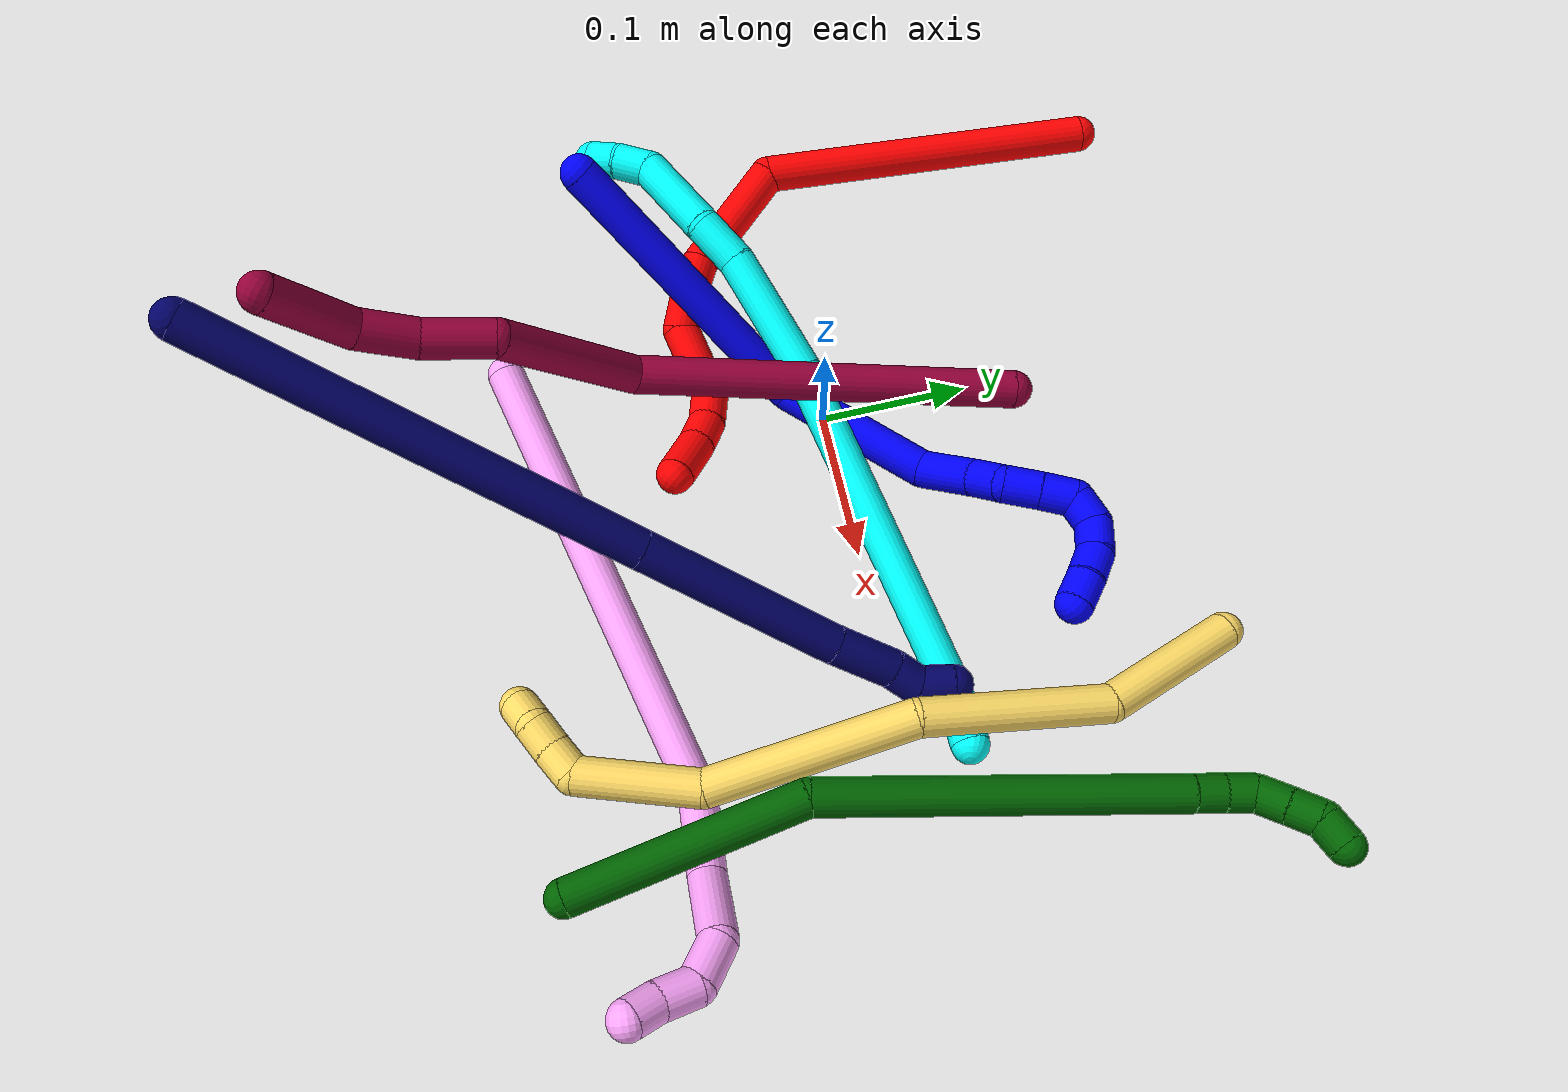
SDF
<sdf version="1.7">
 <world name="default">
  <plugin name="TubeGeneratorPlugin" filename="libtube_generator_plugin.so"/>
  <model name="photoneo_s_sensor">
   <static>1</static>
   <pose>0 0 2 1.57079 1.57079 3.14159</pose>
   <link name="link">
    <inertial><mass>0.1</mass></inertial>
    <sensor name="sensor" type="depth">
     <update_rate>30</update_rate>
     <camera>
      <horizontal_fov>1.22</horizontal_fov>
      <image><width>1920</width><height>1200</height><format>B8G8R8</format></image>
      <clip><near>0.1</near><far>4</far></clip>
      <depth_camera><output>points</output></depth_camera>
     </camera>
     <plugin name="camera_plugin" filename="libgazebo_ros_depth_camera.so">
      <baseline>0.2</baseline>
      <alwaysOn>1</alwaysOn>
      <updateRate>0.0</updateRate>
      <cameraName>camera_ir</cameraName>
      <imageTopicName>/camera/color/image_raw</imageTopicName>
      <cameraInfoTopicName>/camera/color/camera_info</cameraInfoTopicName>
      <depthImageTopicName>/camera/depth/image_raw</depthImageTopicName>
      <depthImageCameraInfoTopicName>/camera/depth/camera_info</depthImageCameraInfoTopicName>
      <pointCloudTopicName>/camera/depth/points</pointCloudTopicName>
      <frameName>fr_optical</frameName>
      <pointCloudCutoff>0.1</pointCloudCutoff>
      <pointCloudCutoffMax>2.0</pointCloudCutoffMax>
      <distortionK1>0</distortionK1>
      <distortionK2>0</distortionK2>
      <distortionK3>0</distortionK3>
      <distortionT1>0</distortionT1>
      <distortionT2>0</distortionT2>
      <CxPrime>0</CxPrime>
      <Cx>0</Cx>
      <Cy>0</Cy>
      <focalLength>0</focalLength>
      <hackBaseline>0</hackBaseline>
     </plugin>
    </sensor>
   </link>
  </model>
  <gravity>0 0 -9.8</gravity>
  <magnetic_field>6e-06 2.3e-05 -4.2e-05</magnetic_field>
  <atmosphere type="adiabatic"/>
  <physics name="default_physics" default="0" type="ode">
   <max_step_size>0.003</max_step_size>
   <real_time_factor>1</real_time_factor>
   <real_time_update_rate>1000</real_time_update_rate>
   <max_contacts>10000</max_contacts>
   <ode>
    <solver>
     <type>quick</type>
     <iters>100</iters>
     <sor>1.3</sor>
     <use_dynamic_moi_rescaling>0</use_dynamic_moi_rescaling>
    </solver>
    <constraints>
     <contact_max_correcting_vel>0</contact_max_correcting_vel>
     <contact_surface_layer>0.001</contact_surface_layer>
     <cfm>0</cfm>
     <erp>0.2</erp>
    </constraints>
   </ode>
  </physics>
  <scene><ambient>0.4 0.4 0.4 1</ambient><background>0.7 0.7 0.7 1</background><shadows>0</shadows></scene>
  <audio><device>default</device></audio>
  <spherical_coordinates>
   <surface_model>EARTH_WGS84</surface_model>
   <latitude_deg>0</latitude_deg>
   <longitude_deg>0</longitude_deg>
   <elevation>0</elevation>
   <heading_deg>0</heading_deg>
  </spherical_coordinates>
  <model name="bin">
   <static>1</static>
   <link name="bottom">
    <collision name="collision-bottom">
     <pose>0 0 -0.01 0 -0 0</pose>
     <geometry><box><size>0.8 0.6 0.02</size></box></geometry>
     <surface>
      <friction><ode><mu>100</mu><mu2>100</mu2></ode></friction>
      <contact><collide_bitmask>65535</collide_bitmask></contact>
     </surface>
    </collision>
   </link>
   <link name="west_wall">
    <collision name="collision-west_wall">
     <pose>-0.41 0 0.1 0 -0 0</pose>
     <geometry><box><size>0.02 0.6 0.2</size></box></geometry>
     <surface>
      <friction><ode><mu>100</mu><mu2>100</mu2></ode></friction>
      <contact><collide_bitmask>65535</collide_bitmask></contact>
     </surface>
    </collision>
   </link>
   <link name="east_wall">
    <collision name="collision-east_wall">
     <pose>0.41 0 0.1 0 -0 0</pose>
     <geometry><box><size>0.02 0.6 0.2</size></box></geometry>
     <surface>
      <friction><ode><mu>100</mu><mu2>100</mu2></ode></friction>
      <contact><collide_bitmask>65535</collide_bitmask></contact>
     </surface>
    </collision>
   </link>
   <link name="south_wall">
    <collision name="collision-south_wall">
     <pose>0 -0.31 0.1 0 -0 0</pose>
     <geometry><box><size>0.8 0.02 0.2</size></box></geometry>
     <surface>
      <friction><ode><mu>100</mu><mu2>100</mu2></ode></friction>
      <contact><collide_bitmask>65535</collide_bitmask></contact>
     </surface>
    </collision>
   </link>
   <link name="north_wall">
    <collision name="collision-north_wall">
     <pose>0 0.31 0.1 0 -0 0</pose>
     <geometry><box><size>0.8 0.02 0.2</size></box></geometry>
     <surface>
      <friction><ode><mu>100</mu><mu2>100</mu2></ode></friction>
      <contact><collide_bitmask>65535</collide_bitmask></contact>
     </surface>
    </collision>
   </link>
  </model>
  <model name="1">
   <static>0</static>
   <link name="1">
    <collision name="collision-cylinder-e_1_1_4">
     <pose>0.002412 -0.004543 -0.100355 3.09636 0.024004 0.975644</pose>
     <geometry><cylinder><radius>0.0125</radius><length>0.200973</length></cylinder></geometry>
     <surface>
      <friction><ode><mu>1.16</mu><mu2>1.16</mu2><slip1>0</slip1><slip2>0</slip2></ode></friction>
      <contact><ode><kp>1e+06</kp><kd>1</kd><max_vel>0</max_vel><min_depth>0.001</min_depth></ode></contact>
     </surface>
    </collision>
    <visual name="visual-cylinder-e_1_1_4">
     <pose>0.002412 -0.004543 -0.100355 3.09636 0.024004 0.975644</pose>
     <geometry><cylinder><radius>0.0125</radius><length>0.200973</length></cylinder></geometry>
     <material><ambient>0 0 1 1</ambient></material>
    </visual>
    <collision name="collision-cylinder-e_2_4_5">
     <pose>0.017116 0.018301 -0.245163 -2.58944 0.231215 -0.778003</pose>
     <geometry><cylinder><radius>0.0125</radius><length>0.10728</length></cylinder></geometry>
     <surface>
      <friction><ode><mu>1.16</mu><mu2>1.16</mu2><slip1>0</slip1><slip2>0</slip2></ode></friction>
      <contact><ode><kp>1e+06</kp><kd>1</kd><max_vel>0</max_vel><min_depth>0.001</min_depth></ode></contact>
     </surface>
    </collision>
    <visual name="visual-cylinder-e_2_4_5">
     <pose>0.017116 0.018301 -0.245163 -2.58944 0.231215 -0.778003</pose>
     <geometry><cylinder><radius>0.0125</radius><length>0.10728</length></cylinder></geometry>
     <material><ambient>0 0 1 1</ambient></material>
    </visual>
    <collision name="collision-cylinder-e_3_5_6">
     <pose>0.034408 0.062632 -0.2986 -2.05829 0.255019 -0.41988</pose>
     <geometry><cylinder><radius>0.0125</radius><length>0.039639</length></cylinder></geometry>
     <surface>
      <friction><ode><mu>1.16</mu><mu2>1.16</mu2><slip1>0</slip1><slip2>0</slip2></ode></friction>
      <contact><ode><kp>1e+06</kp><kd>1</kd><max_vel>0</max_vel><min_depth>0.001</min_depth></ode></contact>
     </surface>
    </collision>
    <visual name="visual-cylinder-e_3_5_6">
     <pose>0.034408 0.062632 -0.2986 -2.05829 0.255019 -0.41988</pose>
     <geometry><cylinder><radius>0.0125</radius><length>0.039639</length></cylinder></geometry>
     <material><ambient>0 0 1 1</ambient></material>
    </visual>
    <collision name="collision-cylinder-e_4_6_7">
     <pose>0.043514 0.089275 -0.311739 -1.97561 0.371149 -0.554694</pose>
     <geometry><cylinder><radius>0.0125</radius><length>0.022643</length></cylinder></geometry>
     <surface>
      <friction><ode><mu>1.16</mu><mu2>1.16</mu2><slip1>0</slip1><slip2>0</slip2></ode></friction>
      <contact><ode><kp>1e+06</kp><kd>1</kd><max_vel>0</max_vel><min_depth>0.001</min_depth></ode></contact>
     </surface>
    </collision>
    <visual name="visual-cylinder-e_4_6_7">
     <pose>0.043514 0.089275 -0.311739 -1.97561 0.371149 -0.554694</pose>
     <geometry><cylinder><radius>0.0125</radius><length>0.022643</length></cylinder></geometry>
     <material><ambient>0 0 1 1</ambient></material>
    </visual>
    <collision name="collision-cylinder-e_5_7_8">
     <pose>0.046689 0.10698 -0.325044 -2.42266 -0.076394 0.20269</pose>
     <geometry><cylinder><radius>0.0125</radius><length>0.024388</length></cylinder></geometry>
     <surface>
      <friction><ode><mu>1.16</mu><mu2>1.16</mu2><slip1>0</slip1><slip2>0</slip2></ode></friction>
      <contact><ode><kp>1e+06</kp><kd>1</kd><max_vel>0</max_vel><min_depth>0.001</min_depth></ode></contact>
     </surface>
    </collision>
    <visual name="visual-cylinder-e_5_7_8">
     <pose>0.046689 0.10698 -0.325044 -2.42266 -0.076394 0.20269</pose>
     <geometry><cylinder><radius>0.0125</radius><length>0.024388</length></cylinder></geometry>
     <material><ambient>0 0 1 1</ambient></material>
    </visual>
    <collision name="collision-cylinder-e_6_8_9">
     <pose>0.044982 0.122081 -0.342994 -2.46319 -0.0686 0.19389</pose>
     <geometry><cylinder><radius>0.0125</radius><length>0.02266</length></cylinder></geometry>
     <surface>
      <friction><ode><mu>1.16</mu><mu2>1.16</mu2><slip1>0</slip1><slip2>0</slip2></ode></friction>
      <contact><ode><kp>1e+06</kp><kd>1</kd><max_vel>0</max_vel><min_depth>0.001</min_depth></ode></contact>
     </surface>
    </collision>
    <visual name="visual-cylinder-e_6_8_9">
     <pose>0.044982 0.122081 -0.342994 -2.46319 -0.0686 0.19389</pose>
     <geometry><cylinder><radius>0.0125</radius><length>0.02266</length></cylinder></geometry>
     <material><ambient>0 0 1 1</ambient></material>
    </visual>
    <collision name="collision-cylinder-e_7_9_10">
     <pose>0.050072 0.131604 -0.35965 -2.84165 0.619669 -2.25962</pose>
     <geometry><cylinder><radius>0.0125</radius><length>0.020203</length></cylinder></geometry>
     <surface>
      <friction><ode><mu>1.16</mu><mu2>1.16</mu2><slip1>0</slip1><slip2>0</slip2></ode></friction>
      <contact><ode><kp>1e+06</kp><kd>1</kd><max_vel>0</max_vel><min_depth>0.001</min_depth></ode></contact>
     </surface>
    </collision>
    <visual name="visual-cylinder-e_7_9_10">
     <pose>0.050072 0.131604 -0.35965 -2.84165 0.619669 -2.25962</pose>
     <geometry><cylinder><radius>0.0125</radius><length>0.020203</length></cylinder></geometry>
     <material><ambient>0 0 1 1</ambient></material>
    </visual>
    <collision name="collision-cylinder-e_8_10_11">
     <pose>0.066298 0.134445 -0.370569 -3.008 1.28088 -2.96254</pose>
     <geometry><cylinder><radius>0.0125</radius><length>0.021621</length></cylinder></geometry>
     <surface>
      <friction><ode><mu>1.16</mu><mu2>1.16</mu2><slip1>0</slip1><slip2>0</slip2></ode></friction>
      <contact><ode><kp>1e+06</kp><kd>1</kd><max_vel>0</max_vel><min_depth>0.001</min_depth></ode></contact>
     </surface>
    </collision>
    <visual name="visual-cylinder-e_8_10_11">
     <pose>0.066298 0.134445 -0.370569 -3.008 1.28088 -2.96254</pose>
     <geometry><cylinder><radius>0.0125</radius><length>0.021621</length></cylinder></geometry>
     <material><ambient>0 0 1 1</ambient></material>
    </visual>
    <collision name="collision-cylinder-e_9_11_12">
     <pose>0.086579 0.133026 -0.373818 1.67191 1.38746 1.4878</pose>
     <geometry><cylinder><radius>0.0125</radius><length>0.020181</length></cylinder></geometry>
     <surface>
      <friction><ode><mu>1.16</mu><mu2>1.16</mu2><slip1>0</slip1><slip2>0</slip2></ode></friction>
      <contact><ode><kp>1e+06</kp><kd>1</kd><max_vel>0</max_vel><min_depth>0.001</min_depth></ode></contact>
     </surface>
    </collision>
    <visual name="visual-cylinder-e_9_11_12">
     <pose>0.086579 0.133026 -0.373818 1.67191 1.38746 1.4878</pose>
     <geometry><cylinder><radius>0.0125</radius><length>0.020181</length></cylinder></geometry>
     <material><ambient>0 0 1 1</ambient></material>
    </visual>
    <collision name="collision-cylinder-e_10_12_2">
     <pose>0.106214 0.128092 -0.374409 1.70059 1.25903 1.38509</pose>
     <geometry><cylinder><radius>0.0125</radius><length>0.020412</length></cylinder></geometry>
     <surface>
      <friction><ode><mu>1.16</mu><mu2>1.16</mu2><slip1>0</slip1><slip2>0</slip2></ode></friction>
      <contact><ode><kp>1e+06</kp><kd>1</kd><max_vel>0</max_vel><min_depth>0.001</min_depth></ode></contact>
     </surface>
    </collision>
    <visual name="visual-cylinder-e_10_12_2">
     <pose>0.106214 0.128092 -0.374409 1.70059 1.25903 1.38509</pose>
     <geometry><cylinder><radius>0.0125</radius><length>0.020412</length></cylinder></geometry>
     <material><ambient>0 0 1 1</ambient></material>
    </visual>
    <collision name="collision-sphere-2">
     <pose>0.115928 0.124987 -0.374814 0 -0 0</pose>
     <geometry><sphere><radius>0.0125</radius></sphere></geometry>
     <surface>
      <friction><ode><mu>1.16</mu><mu2>1.16</mu2><slip1>0</slip1><slip2>0</slip2></ode></friction>
      <contact><ode><kp>1e+06</kp><kd>1</kd><max_vel>0</max_vel><min_depth>0.001</min_depth></ode></contact>
     </surface>
    </collision>
    <visual name="visual-sphere-2">
     <pose>0.115928 0.124987 -0.374814 0 -0 0</pose>
     <geometry><sphere><radius>0.0125</radius></sphere></geometry>
     <material><ambient>0 0 1 1</ambient></material>
    </visual>
    <collision name="collision-sphere-12">
     <pose>0.0965 0.131196 -0.374003 0 -0 0</pose>
     <geometry><sphere><radius>0.0125</radius></sphere></geometry>
     <surface>
      <friction><ode><mu>1.16</mu><mu2>1.16</mu2><slip1>0</slip1><slip2>0</slip2></ode></friction>
      <contact><ode><kp>1e+06</kp><kd>1</kd><max_vel>0</max_vel><min_depth>0.001</min_depth></ode></contact>
     </surface>
    </collision>
    <visual name="visual-sphere-12">
     <pose>0.0965 0.131196 -0.374003 0 -0 0</pose>
     <geometry><sphere><radius>0.0125</radius></sphere></geometry>
     <material><ambient>0 0 1 1</ambient></material>
    </visual>
    <collision name="collision-sphere-11">
     <pose>0.076657 0.134856 -0.373632 0 -0 0</pose>
     <geometry><sphere><radius>0.0125</radius></sphere></geometry>
     <surface>
      <friction><ode><mu>1.16</mu><mu2>1.16</mu2><slip1>0</slip1><slip2>0</slip2></ode></friction>
      <contact><ode><kp>1e+06</kp><kd>1</kd><max_vel>0</max_vel><min_depth>0.001</min_depth></ode></contact>
     </surface>
    </collision>
    <visual name="visual-sphere-11">
     <pose>0.076657 0.134856 -0.373632 0 -0 0</pose>
     <geometry><sphere><radius>0.0125</radius></sphere></geometry>
     <material><ambient>0 0 1 1</ambient></material>
    </visual>
    <collision name="collision-sphere-10">
     <pose>0.055938 0.134033 -0.367506 0 -0 0</pose>
     <geometry><sphere><radius>0.0125</radius></sphere></geometry>
     <surface>
      <friction><ode><mu>1.16</mu><mu2>1.16</mu2><slip1>0</slip1><slip2>0</slip2></ode></friction>
      <contact><ode><kp>1e+06</kp><kd>1</kd><max_vel>0</max_vel><min_depth>0.001</min_depth></ode></contact>
     </surface>
    </collision>
    <visual name="visual-sphere-10">
     <pose>0.055938 0.134033 -0.367506 0 -0 0</pose>
     <geometry><sphere><radius>0.0125</radius></sphere></geometry>
     <material><ambient>0 0 1 1</ambient></material>
    </visual>
    <collision name="collision-sphere-9">
     <pose>0.044205 0.129174 -0.351794 0 -0 0</pose>
     <geometry><sphere><radius>0.0125</radius></sphere></geometry>
     <surface>
      <friction><ode><mu>1.16</mu><mu2>1.16</mu2><slip1>0</slip1><slip2>0</slip2></ode></friction>
      <contact><ode><kp>1e+06</kp><kd>1</kd><max_vel>0</max_vel><min_depth>0.001</min_depth></ode></contact>
     </surface>
    </collision>
    <visual name="visual-sphere-9">
     <pose>0.044205 0.129174 -0.351794 0 -0 0</pose>
     <geometry><sphere><radius>0.0125</radius></sphere></geometry>
     <material><ambient>0 0 1 1</ambient></material>
    </visual>
    <collision name="collision-sphere-4">
     <pose>0.004824 -0.009085 -0.200709 0 -0 0</pose>
     <geometry><sphere><radius>0.0125</radius></sphere></geometry>
     <surface>
      <friction><ode><mu>1.16</mu><mu2>1.16</mu2><slip1>0</slip1><slip2>0</slip2></ode></friction>
      <contact><ode><kp>1e+06</kp><kd>1</kd><max_vel>0</max_vel><min_depth>0.001</min_depth></ode></contact>
     </surface>
    </collision>
    <visual name="visual-sphere-4">
     <pose>0.004824 -0.009085 -0.200709 0 -0 0</pose>
     <geometry><sphere><radius>0.0125</radius></sphere></geometry>
     <material><ambient>0 0 1 1</ambient></material>
    </visual>
    <collision name="collision-sphere-1">
     <geometry><sphere><radius>0.0125</radius></sphere></geometry>
     <surface>
      <friction><ode><mu>1.16</mu><mu2>1.16</mu2><slip1>0</slip1><slip2>0</slip2></ode></friction>
      <contact><ode><kp>1e+06</kp><kd>1</kd><max_vel>0</max_vel><min_depth>0.001</min_depth></ode></contact>
     </surface>
    </collision>
    <visual name="visual-sphere-1">
     <geometry><sphere><radius>0.0125</radius></sphere></geometry>
     <material><ambient>0 0 1 1</ambient></material>
    </visual>
    <collision name="collision-sphere-8">
     <pose>0.045758 0.114987 -0.334193 0 -0 0</pose>
     <geometry><sphere><radius>0.0125</radius></sphere></geometry>
     <surface>
      <friction><ode><mu>1.16</mu><mu2>1.16</mu2><slip1>0</slip1><slip2>0</slip2></ode></friction>
      <contact><ode><kp>1e+06</kp><kd>1</kd><max_vel>0</max_vel><min_depth>0.001</min_depth></ode></contact>
     </surface>
    </collision>
    <visual name="visual-sphere-8">
     <pose>0.045758 0.114987 -0.334193 0 -0 0</pose>
     <geometry><sphere><radius>0.0125</radius></sphere></geometry>
     <material><ambient>0 0 1 1</ambient></material>
    </visual>
    <collision name="collision-sphere-5">
     <pose>0.029408 0.045688 -0.289617 0 -0 0</pose>
     <geometry><sphere><radius>0.0125</radius></sphere></geometry>
     <surface>
      <friction><ode><mu>1.16</mu><mu2>1.16</mu2><slip1>0</slip1><slip2>0</slip2></ode></friction>
      <contact><ode><kp>1e+06</kp><kd>1</kd><max_vel>0</max_vel><min_depth>0.001</min_depth></ode></contact>
     </surface>
    </collision>
    <visual name="visual-sphere-5">
     <pose>0.029408 0.045688 -0.289617 0 -0 0</pose>
     <geometry><sphere><radius>0.0125</radius></sphere></geometry>
     <material><ambient>0 0 1 1</ambient></material>
    </visual>
    <collision name="collision-sphere-6">
     <pose>0.039407 0.079577 -0.307584 0 -0 0</pose>
     <geometry><sphere><radius>0.0125</radius></sphere></geometry>
     <surface>
      <friction><ode><mu>1.16</mu><mu2>1.16</mu2><slip1>0</slip1><slip2>0</slip2></ode></friction>
      <contact><ode><kp>1e+06</kp><kd>1</kd><max_vel>0</max_vel><min_depth>0.001</min_depth></ode></contact>
     </surface>
    </collision>
    <visual name="visual-sphere-6">
     <pose>0.039407 0.079577 -0.307584 0 -0 0</pose>
     <geometry><sphere><radius>0.0125</radius></sphere></geometry>
     <material><ambient>0 0 1 1</ambient></material>
    </visual>
    <collision name="collision-sphere-7">
     <pose>0.04762 0.098972 -0.315894 0 -0 0</pose>
     <geometry><sphere><radius>0.0125</radius></sphere></geometry>
     <surface>
      <friction><ode><mu>1.16</mu><mu2>1.16</mu2><slip1>0</slip1><slip2>0</slip2></ode></friction>
      <contact><ode><kp>1e+06</kp><kd>1</kd><max_vel>0</max_vel><min_depth>0.001</min_depth></ode></contact>
     </surface>
    </collision>
    <visual name="visual-sphere-7">
     <pose>0.04762 0.098972 -0.315894 0 -0 0</pose>
     <geometry><sphere><radius>0.0125</radius></sphere></geometry>
     <material><ambient>0 0 1 1</ambient></material>
    </visual>
    <inertial>
     <pose>0.026377 0.04359 -0.223057 0 -0 0</pose>
     <mass>0.5</mass>
     <inertia>
      <ixx>0.000967</ixx>
      <ixy>0</ixy>
      <ixz>0</ixz>
      <iyy>6.2e-05</iyy>
      <iyz>0</iyz>
      <izz>-0.000111</izz>
     </inertia>
    </inertial>
   </link>
   <pose>-0.147863 -0.123817 0.128376 0.918235 -0.402626 -0.541233</pose>
  </model>
  <model name="2">
   <static>0</static>
   <link name="2">
    <collision name="collision-cylinder-e_1_1_4">
     <pose>0.044159 -0.078227 0.070506 0.837261 0.39705 0.178542</pose>
     <geometry><cylinder><radius>0.0125</radius><length>0.22839</length></cylinder></geometry>
     <surface>
      <friction><ode><mu>1.16</mu><mu2>1.16</mu2><slip1>0</slip1><slip2>0</slip2></ode></friction>
      <contact><ode><kp>1e+06</kp><kd>1</kd><max_vel>0</max_vel><min_depth>0.001</min_depth></ode></contact>
     </surface>
    </collision>
    <visual name="visual-cylinder-e_1_1_4">
     <pose>0.044159 -0.078227 0.070506 0.837261 0.39705 0.178542</pose>
     <geometry><cylinder><radius>0.0125</radius><length>0.22839</length></cylinder></geometry>
     <material><ambient>1 0 0 1</ambient></material>
    </visual>
    <collision name="collision-cylinder-e_2_4_5">
     <pose>0.104609 -0.193443 0.136747 1.68561 0.412411 0.46103</pose>
     <geometry><cylinder><radius>0.0125</radius><length>0.081285</length></cylinder></geometry>
     <surface>
      <friction><ode><mu>1.16</mu><mu2>1.16</mu2><slip1>0</slip1><slip2>0</slip2></ode></friction>
      <contact><ode><kp>1e+06</kp><kd>1</kd><max_vel>0</max_vel><min_depth>0.001</min_depth></ode></contact>
     </surface>
    </collision>
    <visual name="visual-cylinder-e_2_4_5">
     <pose>0.104609 -0.193443 0.136747 1.68561 0.412411 0.46103</pose>
     <geometry><cylinder><radius>0.0125</radius><length>0.081285</length></cylinder></geometry>
     <material><ambient>1 0 0 1</ambient></material>
    </visual>
    <collision name="collision-cylinder-e_3_5_6">
     <pose>0.134838 -0.239312 0.124642 2.29406 0.866455 1.59583</pose>
     <geometry><cylinder><radius>0.0125</radius><length>0.036582</length></cylinder></geometry>
     <surface>
      <friction><ode><mu>1.16</mu><mu2>1.16</mu2><slip1>0</slip1><slip2>0</slip2></ode></friction>
      <contact><ode><kp>1e+06</kp><kd>1</kd><max_vel>0</max_vel><min_depth>0.001</min_depth></ode></contact>
     </surface>
    </collision>
    <visual name="visual-cylinder-e_3_5_6">
     <pose>0.134838 -0.239312 0.124642 2.29406 0.866455 1.59583</pose>
     <geometry><cylinder><radius>0.0125</radius><length>0.036582</length></cylinder></geometry>
     <material><ambient>1 0 0 1</ambient></material>
    </visual>
    <collision name="collision-cylinder-e_4_6_7">
     <pose>0.151626 -0.257352 0.111375 2.10574 0.261536 0.453678</pose>
     <geometry><cylinder><radius>0.0125</radius><length>0.022047</length></cylinder></geometry>
     <surface>
      <friction><ode><mu>1.16</mu><mu2>1.16</mu2><slip1>0</slip1><slip2>0</slip2></ode></friction>
      <contact><ode><kp>1e+06</kp><kd>1</kd><max_vel>0</max_vel><min_depth>0.001</min_depth></ode></contact>
     </surface>
    </collision>
    <visual name="visual-cylinder-e_4_6_7">
     <pose>0.151626 -0.257352 0.111375 2.10574 0.261536 0.453678</pose>
     <geometry><cylinder><radius>0.0125</radius><length>0.022047</length></cylinder></geometry>
     <material><ambient>1 0 0 1</ambient></material>
    </visual>
    <collision name="collision-cylinder-e_5_7_8">
     <pose>0.160027 -0.27515 0.083024 2.78124 0.222833 1.1016</pose>
     <geometry><cylinder><radius>0.0125</radius><length>0.050234</length></cylinder></geometry>
     <surface>
      <friction><ode><mu>1.16</mu><mu2>1.16</mu2><slip1>0</slip1><slip2>0</slip2></ode></friction>
      <contact><ode><kp>1e+06</kp><kd>1</kd><max_vel>0</max_vel><min_depth>0.001</min_depth></ode></contact>
     </surface>
    </collision>
    <visual name="visual-cylinder-e_5_7_8">
     <pose>0.160027 -0.27515 0.083024 2.78124 0.222833 1.1016</pose>
     <geometry><cylinder><radius>0.0125</radius><length>0.050234</length></cylinder></geometry>
     <material><ambient>1 0 0 1</ambient></material>
    </visual>
    <collision name="collision-cylinder-e_6_8_9">
     <pose>0.174145 -0.289466 0.053288 2.44674 0.768028 1.68022</pose>
     <geometry><cylinder><radius>0.0125</radius><length>0.024663</length></cylinder></geometry>
     <surface>
      <friction><ode><mu>1.16</mu><mu2>1.16</mu2><slip1>0</slip1><slip2>0</slip2></ode></friction>
      <contact><ode><kp>1e+06</kp><kd>1</kd><max_vel>0</max_vel><min_depth>0.001</min_depth></ode></contact>
     </surface>
    </collision>
    <visual name="visual-cylinder-e_6_8_9">
     <pose>0.174145 -0.289466 0.053288 2.44674 0.768028 1.68022</pose>
     <geometry><cylinder><radius>0.0125</radius><length>0.024663</length></cylinder></geometry>
     <material><ambient>1 0 0 1</ambient></material>
    </visual>
    <collision name="collision-cylinder-e_7_9_10">
     <pose>0.19195 -0.300532 0.042936 2.15205 0.961648 1.53711</pose>
     <geometry><cylinder><radius>0.0125</radius><length>0.022529</length></cylinder></geometry>
     <surface>
      <friction><ode><mu>1.16</mu><mu2>1.16</mu2><slip1>0</slip1><slip2>0</slip2></ode></friction>
      <contact><ode><kp>1e+06</kp><kd>1</kd><max_vel>0</max_vel><min_depth>0.001</min_depth></ode></contact>
     </surface>
    </collision>
    <visual name="visual-cylinder-e_7_9_10">
     <pose>0.19195 -0.300532 0.042936 2.15205 0.961648 1.53711</pose>
     <geometry><cylinder><radius>0.0125</radius><length>0.022529</length></cylinder></geometry>
     <material><ambient>1 0 0 1</ambient></material>
    </visual>
    <collision name="collision-cylinder-e_8_10_2">
     <pose>0.21623 -0.313311 0.035832 2.02021 1.07134 1.51456</pose>
     <geometry><cylinder><radius>0.0125</radius><length>0.03427</length></cylinder></geometry>
     <surface>
      <friction><ode><mu>1.16</mu><mu2>1.16</mu2><slip1>0</slip1><slip2>0</slip2></ode></friction>
      <contact><ode><kp>1e+06</kp><kd>1</kd><max_vel>0</max_vel><min_depth>0.001</min_depth></ode></contact>
     </surface>
    </collision>
    <visual name="visual-cylinder-e_8_10_2">
     <pose>0.21623 -0.313311 0.035832 2.02021 1.07134 1.51456</pose>
     <geometry><cylinder><radius>0.0125</radius><length>0.03427</length></cylinder></geometry>
     <material><ambient>1 0 0 1</ambient></material>
    </visual>
    <collision name="collision-sphere-2">
     <pose>0.231272 -0.320703 0.032266 0 -0 0</pose>
     <geometry><sphere><radius>0.0125</radius></sphere></geometry>
     <surface>
      <friction><ode><mu>1.16</mu><mu2>1.16</mu2><slip1>0</slip1><slip2>0</slip2></ode></friction>
      <contact><ode><kp>1e+06</kp><kd>1</kd><max_vel>0</max_vel><min_depth>0.001</min_depth></ode></contact>
     </surface>
    </collision>
    <visual name="visual-sphere-2">
     <pose>0.231272 -0.320703 0.032266 0 -0 0</pose>
     <geometry><sphere><radius>0.0125</radius></sphere></geometry>
     <material><ambient>1 0 0 1</ambient></material>
    </visual>
    <collision name="collision-sphere-10">
     <pose>0.201189 -0.305919 0.039397 0 -0 0</pose>
     <geometry><sphere><radius>0.0125</radius></sphere></geometry>
     <surface>
      <friction><ode><mu>1.16</mu><mu2>1.16</mu2><slip1>0</slip1><slip2>0</slip2></ode></friction>
      <contact><ode><kp>1e+06</kp><kd>1</kd><max_vel>0</max_vel><min_depth>0.001</min_depth></ode></contact>
     </surface>
    </collision>
    <visual name="visual-sphere-10">
     <pose>0.201189 -0.305919 0.039397 0 -0 0</pose>
     <geometry><sphere><radius>0.0125</radius></sphere></geometry>
     <material><ambient>1 0 0 1</ambient></material>
    </visual>
    <collision name="collision-sphere-9">
     <pose>0.182711 -0.295145 0.046475 0 -0 0</pose>
     <geometry><sphere><radius>0.0125</radius></sphere></geometry>
     <surface>
      <friction><ode><mu>1.16</mu><mu2>1.16</mu2><slip1>0</slip1><slip2>0</slip2></ode></friction>
      <contact><ode><kp>1e+06</kp><kd>1</kd><max_vel>0</max_vel><min_depth>0.001</min_depth></ode></contact>
     </surface>
    </collision>
    <visual name="visual-sphere-9">
     <pose>0.182711 -0.295145 0.046475 0 -0 0</pose>
     <geometry><sphere><radius>0.0125</radius></sphere></geometry>
     <material><ambient>1 0 0 1</ambient></material>
    </visual>
    <collision name="collision-sphere-4">
     <pose>0.088318 -0.156453 0.141012 0 -0 0</pose>
     <geometry><sphere><radius>0.0125</radius></sphere></geometry>
     <surface>
      <friction><ode><mu>1.16</mu><mu2>1.16</mu2><slip1>0</slip1><slip2>0</slip2></ode></friction>
      <contact><ode><kp>1e+06</kp><kd>1</kd><max_vel>0</max_vel><min_depth>0.001</min_depth></ode></contact>
     </surface>
    </collision>
    <visual name="visual-sphere-4">
     <pose>0.088318 -0.156453 0.141012 0 -0 0</pose>
     <geometry><sphere><radius>0.0125</radius></sphere></geometry>
     <material><ambient>1 0 0 1</ambient></material>
    </visual>
    <collision name="collision-sphere-1">
     <geometry><sphere><radius>0.0125</radius></sphere></geometry>
     <surface>
      <friction><ode><mu>1.16</mu><mu2>1.16</mu2><slip1>0</slip1><slip2>0</slip2></ode></friction>
      <contact><ode><kp>1e+06</kp><kd>1</kd><max_vel>0</max_vel><min_depth>0.001</min_depth></ode></contact>
     </surface>
    </collision>
    <visual name="visual-sphere-1">
     <geometry><sphere><radius>0.0125</radius></sphere></geometry>
     <material><ambient>1 0 0 1</ambient></material>
    </visual>
    <collision name="collision-sphere-8">
     <pose>0.165578 -0.283787 0.060101 0 -0 0</pose>
     <geometry><sphere><radius>0.0125</radius></sphere></geometry>
     <surface>
      <friction><ode><mu>1.16</mu><mu2>1.16</mu2><slip1>0</slip1><slip2>0</slip2></ode></friction>
      <contact><ode><kp>1e+06</kp><kd>1</kd><max_vel>0</max_vel><min_depth>0.001</min_depth></ode></contact>
     </surface>
    </collision>
    <visual name="visual-sphere-8">
     <pose>0.165578 -0.283787 0.060101 0 -0 0</pose>
     <geometry><sphere><radius>0.0125</radius></sphere></geometry>
     <material><ambient>1 0 0 1</ambient></material>
    </visual>
    <collision name="collision-sphere-5">
     <pose>0.120899 -0.230433 0.132481 0 -0 0</pose>
     <geometry><sphere><radius>0.0125</radius></sphere></geometry>
     <surface>
      <friction><ode><mu>1.16</mu><mu2>1.16</mu2><slip1>0</slip1><slip2>0</slip2></ode></friction>
      <contact><ode><kp>1e+06</kp><kd>1</kd><max_vel>0</max_vel><min_depth>0.001</min_depth></ode></contact>
     </surface>
    </collision>
    <visual name="visual-sphere-5">
     <pose>0.120899 -0.230433 0.132481 0 -0 0</pose>
     <geometry><sphere><radius>0.0125</radius></sphere></geometry>
     <material><ambient>1 0 0 1</ambient></material>
    </visual>
    <collision name="collision-sphere-6">
     <pose>0.148776 -0.248191 0.116804 0 -0 0</pose>
     <geometry><sphere><radius>0.0125</radius></sphere></geometry>
     <surface>
      <friction><ode><mu>1.16</mu><mu2>1.16</mu2><slip1>0</slip1><slip2>0</slip2></ode></friction>
      <contact><ode><kp>1e+06</kp><kd>1</kd><max_vel>0</max_vel><min_depth>0.001</min_depth></ode></contact>
     </surface>
    </collision>
    <visual name="visual-sphere-6">
     <pose>0.148776 -0.248191 0.116804 0 -0 0</pose>
     <geometry><sphere><radius>0.0125</radius></sphere></geometry>
     <material><ambient>1 0 0 1</ambient></material>
    </visual>
    <collision name="collision-sphere-7">
     <pose>0.154476 -0.266513 0.105946 0 -0 0</pose>
     <geometry><sphere><radius>0.0125</radius></sphere></geometry>
     <surface>
      <friction><ode><mu>1.16</mu><mu2>1.16</mu2><slip1>0</slip1><slip2>0</slip2></ode></friction>
      <contact><ode><kp>1e+06</kp><kd>1</kd><max_vel>0</max_vel><min_depth>0.001</min_depth></ode></contact>
     </surface>
    </collision>
    <visual name="visual-sphere-7">
     <pose>0.154476 -0.266513 0.105946 0 -0 0</pose>
     <geometry><sphere><radius>0.0125</radius></sphere></geometry>
     <material><ambient>1 0 0 1</ambient></material>
    </visual>
    <inertial>
     <pose>0.101865 -0.172975 0.083827 0 -0 0</pose>
     <mass>0.5</mass>
     <inertia>
      <ixx>0.001177</ixx>
      <ixy>0</ixy>
      <ixz>0</ixz>
      <iyy>0.000897</iyy>
      <iyz>0</iyz>
      <izz>0.000324</izz>
     </inertia>
    </inertial>
   </link>
   <pose>-0.170132 0.232157 0.011666 1.31181 -1.00429 -0.740061</pose>
  </model>
  <model name="3">
   <static>0</static>
   <link name="3">
    <collision name="collision-cylinder-e_1_1_4">
     <pose>-0.00609 -0.001461 -0.018527 3.06292 -0.316646 -2.65822</pose>
     <geometry><cylinder><radius>0.0125</radius><length>0.039114</length></cylinder></geometry>
     <surface>
      <friction><ode><mu>1.16</mu><mu2>1.16</mu2><slip1>0</slip1><slip2>0</slip2></ode></friction>
      <contact><ode><kp>1e+06</kp><kd>1</kd><max_vel>0</max_vel><min_depth>0.001</min_depth></ode></contact>
     </surface>
    </collision>
    <visual name="visual-cylinder-e_1_1_4">
     <pose>-0.00609 -0.001461 -0.018527 3.06292 -0.316646 -2.65822</pose>
     <geometry><cylinder><radius>0.0125</radius><length>0.039114</length></cylinder></geometry>
     <material><ambient>0.003922 1 0.996078 1</ambient></material>
    </visual>
    <collision name="collision-cylinder-e_2_4_5">
     <pose>-0.084536 -0.001102 -0.128209 -3.12163 -0.670842 3.08435</pose>
     <geometry><cylinder><radius>0.0125</radius><length>0.232791</length></cylinder></geometry>
     <surface>
      <friction><ode><mu>1.16</mu><mu2>1.16</mu2><slip1>0</slip1><slip2>0</slip2></ode></friction>
      <contact><ode><kp>1e+06</kp><kd>1</kd><max_vel>0</max_vel><min_depth>0.001</min_depth></ode></contact>
     </surface>
    </collision>
    <visual name="visual-cylinder-e_2_4_5">
     <pose>-0.084536 -0.001102 -0.128209 -3.12163 -0.670842 3.08435</pose>
     <geometry><cylinder><radius>0.0125</radius><length>0.232791</length></cylinder></geometry>
     <material><ambient>0.003922 1 0.996078 1</ambient></material>
    </visual>
    <collision name="collision-cylinder-e_3_5_6">
     <pose>-0.187599 -0.001217 -0.250776 3.08007 -0.773073 -2.99067</pose>
     <geometry><cylinder><radius>0.0125</radius><length>0.087939</length></cylinder></geometry>
     <surface>
      <friction><ode><mu>1.16</mu><mu2>1.16</mu2><slip1>0</slip1><slip2>0</slip2></ode></friction>
      <contact><ode><kp>1e+06</kp><kd>1</kd><max_vel>0</max_vel><min_depth>0.001</min_depth></ode></contact>
     </surface>
    </collision>
    <visual name="visual-cylinder-e_3_5_6">
     <pose>-0.187599 -0.001217 -0.250776 3.08007 -0.773073 -2.99067</pose>
     <geometry><cylinder><radius>0.0125</radius><length>0.087939</length></cylinder></geometry>
     <material><ambient>0.003922 1 0.996078 1</ambient></material>
    </visual>
    <collision name="collision-cylinder-e_4_6_7">
     <pose>-0.23184 -0.006142 -0.29203 2.84673 -0.920982 -2.55982</pose>
     <geometry><cylinder><radius>0.0125</radius><length>0.034</length></cylinder></geometry>
     <surface>
      <friction><ode><mu>1.16</mu><mu2>1.16</mu2><slip1>0</slip1><slip2>0</slip2></ode></friction>
      <contact><ode><kp>1e+06</kp><kd>1</kd><max_vel>0</max_vel><min_depth>0.001</min_depth></ode></contact>
     </surface>
    </collision>
    <visual name="visual-cylinder-e_4_6_7">
     <pose>-0.23184 -0.006142 -0.29203 2.84673 -0.920982 -2.55982</pose>
     <geometry><cylinder><radius>0.0125</radius><length>0.034</length></cylinder></geometry>
     <material><ambient>0.003922 1 0.996078 1</ambient></material>
    </visual>
    <collision name="collision-cylinder-e_5_7_8">
     <pose>-0.263586 -0.019009 -0.32492 2.73669 -0.628118 -2.01443</pose>
     <geometry><cylinder><radius>0.0125</radius><length>0.061981</length></cylinder></geometry>
     <surface>
      <friction><ode><mu>1.16</mu><mu2>1.16</mu2><slip1>0</slip1><slip2>0</slip2></ode></friction>
      <contact><ode><kp>1e+06</kp><kd>1</kd><max_vel>0</max_vel><min_depth>0.001</min_depth></ode></contact>
     </surface>
    </collision>
    <visual name="visual-cylinder-e_5_7_8">
     <pose>-0.263586 -0.019009 -0.32492 2.73669 -0.628118 -2.01443</pose>
     <geometry><cylinder><radius>0.0125</radius><length>0.061981</length></cylinder></geometry>
     <material><ambient>0.003922 1 0.996078 1</ambient></material>
    </visual>
    <collision name="collision-cylinder-e_6_8_9">
     <pose>-0.290233 -0.036512 -0.351678 2.02365 -0.782825 -1.16644</pose>
     <geometry><cylinder><radius>0.0125</radius><length>0.023924</length></cylinder></geometry>
     <surface>
      <friction><ode><mu>1.16</mu><mu2>1.16</mu2><slip1>0</slip1><slip2>0</slip2></ode></friction>
      <contact><ode><kp>1e+06</kp><kd>1</kd><max_vel>0</max_vel><min_depth>0.001</min_depth></ode></contact>
     </surface>
    </collision>
    <visual name="visual-cylinder-e_6_8_9">
     <pose>-0.290233 -0.036512 -0.351678 2.02365 -0.782825 -1.16644</pose>
     <geometry><cylinder><radius>0.0125</radius><length>0.023924</length></cylinder></geometry>
     <material><ambient>0.003922 1 0.996078 1</ambient></material>
    </visual>
    <collision name="collision-cylinder-e_7_9_2">
     <pose>-0.304333 -0.051937 -0.35849 1.94935 -0.593548 -0.846933</pose>
     <geometry><cylinder><radius>0.0125</radius><length>0.02025</length></cylinder></geometry>
     <surface>
      <friction><ode><mu>1.16</mu><mu2>1.16</mu2><slip1>0</slip1><slip2>0</slip2></ode></friction>
      <contact><ode><kp>1e+06</kp><kd>1</kd><max_vel>0</max_vel><min_depth>0.001</min_depth></ode></contact>
     </surface>
    </collision>
    <visual name="visual-cylinder-e_7_9_2">
     <pose>-0.304333 -0.051937 -0.35849 1.94935 -0.593548 -0.846933</pose>
     <geometry><cylinder><radius>0.0125</radius><length>0.02025</length></cylinder></geometry>
     <material><ambient>0.003922 1 0.996078 1</ambient></material>
    </visual>
    <collision name="collision-sphere-2">
     <pose>-0.309996 -0.059736 -0.361592 0 -0 0</pose>
     <geometry><sphere><radius>0.0125</radius></sphere></geometry>
     <surface>
      <friction><ode><mu>1.16</mu><mu2>1.16</mu2><slip1>0</slip1><slip2>0</slip2></ode></friction>
      <contact><ode><kp>1e+06</kp><kd>1</kd><max_vel>0</max_vel><min_depth>0.001</min_depth></ode></contact>
     </surface>
    </collision>
    <visual name="visual-sphere-2">
     <pose>-0.309996 -0.059736 -0.361592 0 -0 0</pose>
     <geometry><sphere><radius>0.0125</radius></sphere></geometry>
     <material><ambient>0.003922 1 0.996078 1</ambient></material>
    </visual>
    <collision name="collision-sphere-9">
     <pose>-0.29867 -0.044138 -0.355388 0 -0 0</pose>
     <geometry><sphere><radius>0.0125</radius></sphere></geometry>
     <surface>
      <friction><ode><mu>1.16</mu><mu2>1.16</mu2><slip1>0</slip1><slip2>0</slip2></ode></friction>
      <contact><ode><kp>1e+06</kp><kd>1</kd><max_vel>0</max_vel><min_depth>0.001</min_depth></ode></contact>
     </surface>
    </collision>
    <visual name="visual-sphere-9">
     <pose>-0.29867 -0.044138 -0.355388 0 -0 0</pose>
     <geometry><sphere><radius>0.0125</radius></sphere></geometry>
     <material><ambient>0.003922 1 0.996078 1</ambient></material>
    </visual>
    <collision name="collision-sphere-4">
     <pose>-0.01218 -0.002921 -0.037055 0 -0 0</pose>
     <geometry><sphere><radius>0.0125</radius></sphere></geometry>
     <surface>
      <friction><ode><mu>1.16</mu><mu2>1.16</mu2><slip1>0</slip1><slip2>0</slip2></ode></friction>
      <contact><ode><kp>1e+06</kp><kd>1</kd><max_vel>0</max_vel><min_depth>0.001</min_depth></ode></contact>
     </surface>
    </collision>
    <visual name="visual-sphere-4">
     <pose>-0.01218 -0.002921 -0.037055 0 -0 0</pose>
     <geometry><sphere><radius>0.0125</radius></sphere></geometry>
     <material><ambient>0.003922 1 0.996078 1</ambient></material>
    </visual>
    <collision name="collision-sphere-1">
     <geometry><sphere><radius>0.0125</radius></sphere></geometry>
     <surface>
      <friction><ode><mu>1.16</mu><mu2>1.16</mu2><slip1>0</slip1><slip2>0</slip2></ode></friction>
      <contact><ode><kp>1e+06</kp><kd>1</kd><max_vel>0</max_vel><min_depth>0.001</min_depth></ode></contact>
     </surface>
    </collision>
    <visual name="visual-sphere-1">
     <geometry><sphere><radius>0.0125</radius></sphere></geometry>
     <material><ambient>0.003922 1 0.996078 1</ambient></material>
    </visual>
    <collision name="collision-sphere-8">
     <pose>-0.281797 -0.028887 -0.347968 0 -0 0</pose>
     <geometry><sphere><radius>0.0125</radius></sphere></geometry>
     <surface>
      <friction><ode><mu>1.16</mu><mu2>1.16</mu2><slip1>0</slip1><slip2>0</slip2></ode></friction>
      <contact><ode><kp>1e+06</kp><kd>1</kd><max_vel>0</max_vel><min_depth>0.001</min_depth></ode></contact>
     </surface>
    </collision>
    <visual name="visual-sphere-8">
     <pose>-0.281797 -0.028887 -0.347968 0 -0 0</pose>
     <geometry><sphere><radius>0.0125</radius></sphere></geometry>
     <material><ambient>0.003922 1 0.996078 1</ambient></material>
    </visual>
    <collision name="collision-sphere-5">
     <pose>-0.156893 0.000718 -0.219363 0 -0 0</pose>
     <geometry><sphere><radius>0.0125</radius></sphere></geometry>
     <surface>
      <friction><ode><mu>1.16</mu><mu2>1.16</mu2><slip1>0</slip1><slip2>0</slip2></ode></friction>
      <contact><ode><kp>1e+06</kp><kd>1</kd><max_vel>0</max_vel><min_depth>0.001</min_depth></ode></contact>
     </surface>
    </collision>
    <visual name="visual-sphere-5">
     <pose>-0.156893 0.000718 -0.219363 0 -0 0</pose>
     <geometry><sphere><radius>0.0125</radius></sphere></geometry>
     <material><ambient>0.003922 1 0.996078 1</ambient></material>
    </visual>
    <collision name="collision-sphere-6">
     <pose>-0.218305 -0.003153 -0.282188 0 -0 0</pose>
     <geometry><sphere><radius>0.0125</radius></sphere></geometry>
     <surface>
      <friction><ode><mu>1.16</mu><mu2>1.16</mu2><slip1>0</slip1><slip2>0</slip2></ode></friction>
      <contact><ode><kp>1e+06</kp><kd>1</kd><max_vel>0</max_vel><min_depth>0.001</min_depth></ode></contact>
     </surface>
    </collision>
    <visual name="visual-sphere-6">
     <pose>-0.218305 -0.003153 -0.282188 0 -0 0</pose>
     <geometry><sphere><radius>0.0125</radius></sphere></geometry>
     <material><ambient>0.003922 1 0.996078 1</ambient></material>
    </visual>
    <collision name="collision-sphere-7">
     <pose>-0.245375 -0.009131 -0.301872 0 -0 0</pose>
     <geometry><sphere><radius>0.0125</radius></sphere></geometry>
     <surface>
      <friction><ode><mu>1.16</mu><mu2>1.16</mu2><slip1>0</slip1><slip2>0</slip2></ode></friction>
      <contact><ode><kp>1e+06</kp><kd>1</kd><max_vel>0</max_vel><min_depth>0.001</min_depth></ode></contact>
     </surface>
    </collision>
    <visual name="visual-sphere-7">
     <pose>-0.245375 -0.009131 -0.301872 0 -0 0</pose>
     <geometry><sphere><radius>0.0125</radius></sphere></geometry>
     <material><ambient>0.003922 1 0.996078 1</ambient></material>
    </visual>
    <inertial>
     <pose>-0.147482 -0.007466 -0.196729 0 -0 0</pose>
     <mass>0.5</mass>
     <inertia>
      <ixx>-0.000892</ixx>
      <ixy>0</ixy>
      <ixz>0</ixz>
      <iyy>0.001157</iyy>
      <iyz>0</iyz>
      <izz>0.000691</izz>
     </inertia>
    </inertial>
   </link>
   <pose>0.242499 0.034643 0.019365 1.09236 0.668712 0.972904</pose>
  </model>
  <model name="4">
   <static>0</static>
   <link name="4">
    <collision name="collision-cylinder-e_1_1_4">
     <pose>0.062179 -0.003214 0.145124 0.02214 0.404702 0.004542</pose>
     <geometry><cylinder><radius>0.0125</radius><length>0.315833</length></cylinder></geometry>
     <surface>
      <friction><ode><mu>1.16</mu><mu2>1.16</mu2><slip1>0</slip1><slip2>0</slip2></ode></friction>
      <contact><ode><kp>1e+06</kp><kd>1</kd><max_vel>0</max_vel><min_depth>0.001</min_depth></ode></contact>
     </surface>
    </collision>
    <visual name="visual-cylinder-e_1_1_4">
     <pose>0.062179 -0.003214 0.145124 0.02214 0.404702 0.004542</pose>
     <geometry><cylinder><radius>0.0125</radius><length>0.315833</length></cylinder></geometry>
     <material><ambient>1 0.65098 0.996078 1</ambient></material>
    </visual>
    <collision name="collision-cylinder-e_2_4_5">
     <pose>0.128328 -0.001599 0.315246 -0.19078 0.154726 -0.014834</pose>
     <geometry><cylinder><radius>0.0125</radius><length>0.051534</length></cylinder></geometry>
     <surface>
      <friction><ode><mu>1.16</mu><mu2>1.16</mu2><slip1>0</slip1><slip2>0</slip2></ode></friction>
      <contact><ode><kp>1e+06</kp><kd>1</kd><max_vel>0</max_vel><min_depth>0.001</min_depth></ode></contact>
     </surface>
    </collision>
    <visual name="visual-cylinder-e_2_4_5">
     <pose>0.128328 -0.001599 0.315246 -0.19078 0.154726 -0.014834</pose>
     <geometry><cylinder><radius>0.0125</radius><length>0.051534</length></cylinder></geometry>
     <material><ambient>1 0.65098 0.996078 1</ambient></material>
    </visual>
    <collision name="collision-cylinder-e_3_5_6">
     <pose>0.15087 0.018111 0.355029 -0.788667 0.724562 -0.312857</pose>
     <geometry><cylinder><radius>0.0125</radius><length>0.056035</length></cylinder></geometry>
     <surface>
      <friction><ode><mu>1.16</mu><mu2>1.16</mu2><slip1>0</slip1><slip2>0</slip2></ode></friction>
      <contact><ode><kp>1e+06</kp><kd>1</kd><max_vel>0</max_vel><min_depth>0.001</min_depth></ode></contact>
     </surface>
    </collision>
    <visual name="visual-cylinder-e_3_5_6">
     <pose>0.15087 0.018111 0.355029 -0.788667 0.724562 -0.312857</pose>
     <geometry><cylinder><radius>0.0125</radius><length>0.056035</length></cylinder></geometry>
     <material><ambient>1 0.65098 0.996078 1</ambient></material>
    </visual>
    <collision name="collision-cylinder-e_4_6_7">
     <pose>0.171633 0.045174 0.378909 -0.929495 0.143331 -0.071955</pose>
     <geometry><cylinder><radius>0.0125</radius><length>0.030716</length></cylinder></geometry>
     <surface>
      <friction><ode><mu>1.16</mu><mu2>1.16</mu2><slip1>0</slip1><slip2>0</slip2></ode></friction>
      <contact><ode><kp>1e+06</kp><kd>1</kd><max_vel>0</max_vel><min_depth>0.001</min_depth></ode></contact>
     </surface>
    </collision>
    <visual name="visual-cylinder-e_4_6_7">
     <pose>0.171633 0.045174 0.378909 -0.929495 0.143331 -0.071955</pose>
     <geometry><cylinder><radius>0.0125</radius><length>0.030716</length></cylinder></geometry>
     <material><ambient>1 0.65098 0.996078 1</ambient></material>
    </visual>
    <collision name="collision-cylinder-e_5_7_8">
     <pose>0.17024 0.069422 0.389228 -1.46957 -0.287572 0.26017</pose>
     <geometry><cylinder><radius>0.0125</radius><length>0.025297</length></cylinder></geometry>
     <surface>
      <friction><ode><mu>1.16</mu><mu2>1.16</mu2><slip1>0</slip1><slip2>0</slip2></ode></friction>
      <contact><ode><kp>1e+06</kp><kd>1</kd><max_vel>0</max_vel><min_depth>0.001</min_depth></ode></contact>
     </surface>
    </collision>
    <visual name="visual-cylinder-e_5_7_8">
     <pose>0.17024 0.069422 0.389228 -1.46957 -0.287572 0.26017</pose>
     <geometry><cylinder><radius>0.0125</radius><length>0.025297</length></cylinder></geometry>
     <material><ambient>1 0.65098 0.996078 1</ambient></material>
    </visual>
    <collision name="collision-cylinder-e_6_8_2">
     <pose>0.165842 0.09159 0.392257 -1.39413 -0.078835 0.066018</pose>
     <geometry><cylinder><radius>0.0125</radius><length>0.020585</length></cylinder></geometry>
     <surface>
      <friction><ode><mu>1.16</mu><mu2>1.16</mu2><slip1>0</slip1><slip2>0</slip2></ode></friction>
      <contact><ode><kp>1e+06</kp><kd>1</kd><max_vel>0</max_vel><min_depth>0.001</min_depth></ode></contact>
     </surface>
    </collision>
    <visual name="visual-cylinder-e_6_8_2">
     <pose>0.165842 0.09159 0.392257 -1.39413 -0.078835 0.066018</pose>
     <geometry><cylinder><radius>0.0125</radius><length>0.020585</length></cylinder></geometry>
     <material><ambient>1 0.65098 0.996078 1</ambient></material>
    </visual>
    <collision name="collision-sphere-2">
     <pose>0.165031 0.101691 0.39406 0 -0 0</pose>
     <geometry><sphere><radius>0.0125</radius></sphere></geometry>
     <surface>
      <friction><ode><mu>1.16</mu><mu2>1.16</mu2><slip1>0</slip1><slip2>0</slip2></ode></friction>
      <contact><ode><kp>1e+06</kp><kd>1</kd><max_vel>0</max_vel><min_depth>0.001</min_depth></ode></contact>
     </surface>
    </collision>
    <visual name="visual-sphere-2">
     <pose>0.165031 0.101691 0.39406 0 -0 0</pose>
     <geometry><sphere><radius>0.0125</radius></sphere></geometry>
     <material><ambient>1 0.65098 0.996078 1</ambient></material>
    </visual>
    <collision name="collision-sphere-4">
     <pose>0.124357 -0.006427 0.290249 0 -0 0</pose>
     <geometry><sphere><radius>0.0125</radius></sphere></geometry>
     <surface>
      <friction><ode><mu>1.16</mu><mu2>1.16</mu2><slip1>0</slip1><slip2>0</slip2></ode></friction>
      <contact><ode><kp>1e+06</kp><kd>1</kd><max_vel>0</max_vel><min_depth>0.001</min_depth></ode></contact>
     </surface>
    </collision>
    <visual name="visual-sphere-4">
     <pose>0.124357 -0.006427 0.290249 0 -0 0</pose>
     <geometry><sphere><radius>0.0125</radius></sphere></geometry>
     <material><ambient>1 0.65098 0.996078 1</ambient></material>
    </visual>
    <collision name="collision-sphere-1">
     <geometry><sphere><radius>0.0125</radius></sphere></geometry>
     <surface>
      <friction><ode><mu>1.16</mu><mu2>1.16</mu2><slip1>0</slip1><slip2>0</slip2></ode></friction>
      <contact><ode><kp>1e+06</kp><kd>1</kd><max_vel>0</max_vel><min_depth>0.001</min_depth></ode></contact>
     </surface>
    </collision>
    <visual name="visual-sphere-1">
     <geometry><sphere><radius>0.0125</radius></sphere></geometry>
     <material><ambient>1 0.65098 0.996078 1</ambient></material>
    </visual>
    <collision name="collision-sphere-8">
     <pose>0.166652 0.081489 0.390454 0 -0 0</pose>
     <geometry><sphere><radius>0.0125</radius></sphere></geometry>
     <surface>
      <friction><ode><mu>1.16</mu><mu2>1.16</mu2><slip1>0</slip1><slip2>0</slip2></ode></friction>
      <contact><ode><kp>1e+06</kp><kd>1</kd><max_vel>0</max_vel><min_depth>0.001</min_depth></ode></contact>
     </surface>
    </collision>
    <visual name="visual-sphere-8">
     <pose>0.166652 0.081489 0.390454 0 -0 0</pose>
     <geometry><sphere><radius>0.0125</radius></sphere></geometry>
     <material><ambient>1 0.65098 0.996078 1</ambient></material>
    </visual>
    <collision name="collision-sphere-5">
     <pose>0.132299 0.003228 0.340244 0 -0 0</pose>
     <geometry><sphere><radius>0.0125</radius></sphere></geometry>
     <surface>
      <friction><ode><mu>1.16</mu><mu2>1.16</mu2><slip1>0</slip1><slip2>0</slip2></ode></friction>
      <contact><ode><kp>1e+06</kp><kd>1</kd><max_vel>0</max_vel><min_depth>0.001</min_depth></ode></contact>
     </surface>
    </collision>
    <visual name="visual-sphere-5">
     <pose>0.132299 0.003228 0.340244 0 -0 0</pose>
     <geometry><sphere><radius>0.0125</radius></sphere></geometry>
     <material><ambient>1 0.65098 0.996078 1</ambient></material>
    </visual>
    <collision name="collision-sphere-6">
     <pose>0.16944 0.032994 0.369815 0 -0 0</pose>
     <geometry><sphere><radius>0.0125</radius></sphere></geometry>
     <surface>
      <friction><ode><mu>1.16</mu><mu2>1.16</mu2><slip1>0</slip1><slip2>0</slip2></ode></friction>
      <contact><ode><kp>1e+06</kp><kd>1</kd><max_vel>0</max_vel><min_depth>0.001</min_depth></ode></contact>
     </surface>
    </collision>
    <visual name="visual-sphere-6">
     <pose>0.16944 0.032994 0.369815 0 -0 0</pose>
     <geometry><sphere><radius>0.0125</radius></sphere></geometry>
     <material><ambient>1 0.65098 0.996078 1</ambient></material>
    </visual>
    <collision name="collision-sphere-7">
     <pose>0.173827 0.057355 0.388002 0 -0 0</pose>
     <geometry><sphere><radius>0.0125</radius></sphere></geometry>
     <surface>
      <friction><ode><mu>1.16</mu><mu2>1.16</mu2><slip1>0</slip1><slip2>0</slip2></ode></friction>
      <contact><ode><kp>1e+06</kp><kd>1</kd><max_vel>0</max_vel><min_depth>0.001</min_depth></ode></contact>
     </surface>
    </collision>
    <visual name="visual-sphere-7">
     <pose>0.173827 0.057355 0.388002 0 -0 0</pose>
     <geometry><sphere><radius>0.0125</radius></sphere></geometry>
     <material><ambient>1 0.65098 0.996078 1</ambient></material>
    </visual>
    <inertial>
     <pose>0.095395 0.009893 0.223069 0 -0 0</pose>
     <mass>0.5</mass>
     <inertia>
      <ixx>0.002477</ixx>
      <ixy>0</ixy>
      <ixz>0</ixz>
      <iyy>0.002682</iyy>
      <iyz>0</iyz>
      <izz>-0.000985</izz>
     </inertia>
    </inertial>
   </link>
   <pose>-0.0783 -0.204262 0.011499 1.99083 -0.798425 1.19408</pose>
  </model>
  <model name="5">
   <static>0</static>
   <link name="5">
    <collision name="collision-cylinder-e_1_1_4">
     <pose>0.015587 0.000925 0.046092 -0.020066 0.326039 -0.003301</pose>
     <geometry><cylinder><radius>0.0125</radius><length>0.09733</length></cylinder></geometry>
     <surface>
      <friction><ode><mu>1.16</mu><mu2>1.16</mu2><slip1>0</slip1><slip2>0</slip2></ode></friction>
      <contact><ode><kp>1e+06</kp><kd>1</kd><max_vel>0</max_vel><min_depth>0.001</min_depth></ode></contact>
     </surface>
    </collision>
    <visual name="visual-cylinder-e_1_1_4">
     <pose>0.015587 0.000925 0.046092 -0.020066 0.326039 -0.003301</pose>
     <geometry><cylinder><radius>0.0125</radius><length>0.09733</length></cylinder></geometry>
     <material><ambient>1 0.858824 0.4 1</ambient></material>
    </visual>
    <collision name="collision-cylinder-e_2_4_5">
     <pose>0.043192 -0.023821 0.14736 0.435465 0.194975 0.043267</pose>
     <geometry><cylinder><radius>0.0125</radius><length>0.124061</length></cylinder></geometry>
     <surface>
      <friction><ode><mu>1.16</mu><mu2>1.16</mu2><slip1>0</slip1><slip2>0</slip2></ode></friction>
      <contact><ode><kp>1e+06</kp><kd>1</kd><max_vel>0</max_vel><min_depth>0.001</min_depth></ode></contact>
     </surface>
    </collision>
    <visual name="visual-cylinder-e_2_4_5">
     <pose>0.043192 -0.023821 0.14736 0.435465 0.194975 0.043267</pose>
     <geometry><cylinder><radius>0.0125</radius><length>0.124061</length></cylinder></geometry>
     <material><ambient>1 0.858824 0.4 1</ambient></material>
    </visual>
    <collision name="collision-cylinder-e_3_5_6">
     <pose>0.089741 -0.071415 0.257502 0.37952 0.528205 0.103786</pose>
     <geometry><cylinder><radius>0.0125</radius><length>0.13703</length></cylinder></geometry>
     <surface>
      <friction><ode><mu>1.16</mu><mu2>1.16</mu2><slip1>0</slip1><slip2>0</slip2></ode></friction>
      <contact><ode><kp>1e+06</kp><kd>1</kd><max_vel>0</max_vel><min_depth>0.001</min_depth></ode></contact>
     </surface>
    </collision>
    <visual name="visual-cylinder-e_3_5_6">
     <pose>0.089741 -0.071415 0.257502 0.37952 0.528205 0.103786</pose>
     <geometry><cylinder><radius>0.0125</radius><length>0.13703</length></cylinder></geometry>
     <material><ambient>1 0.858824 0.4 1</ambient></material>
    </visual>
    <collision name="collision-cylinder-e_4_6_7">
     <pose>0.134893 -0.119142 0.341356 0.72906 0.267646 0.102653</pose>
     <geometry><cylinder><radius>0.0125</radius><length>0.080326</length></cylinder></geometry>
     <surface>
      <friction><ode><mu>1.16</mu><mu2>1.16</mu2><slip1>0</slip1><slip2>0</slip2></ode></friction>
      <contact><ode><kp>1e+06</kp><kd>1</kd><max_vel>0</max_vel><min_depth>0.001</min_depth></ode></contact>
     </surface>
    </collision>
    <visual name="visual-cylinder-e_4_6_7">
     <pose>0.134893 -0.119142 0.341356 0.72906 0.267646 0.102653</pose>
     <geometry><cylinder><radius>0.0125</radius><length>0.080326</length></cylinder></geometry>
     <material><ambient>1 0.858824 0.4 1</ambient></material>
    </visual>
    <collision name="collision-cylinder-e_5_7_8">
     <pose>0.14444 -0.155327 0.372142 1.38987 -0.101386 -0.084545</pose>
     <geometry><cylinder><radius>0.0125</radius><length>0.02122</length></cylinder></geometry>
     <surface>
      <friction><ode><mu>1.16</mu><mu2>1.16</mu2><slip1>0</slip1><slip2>0</slip2></ode></friction>
      <contact><ode><kp>1e+06</kp><kd>1</kd><max_vel>0</max_vel><min_depth>0.001</min_depth></ode></contact>
     </surface>
    </collision>
    <visual name="visual-cylinder-e_5_7_8">
     <pose>0.14444 -0.155327 0.372142 1.38987 -0.101386 -0.084545</pose>
     <geometry><cylinder><radius>0.0125</radius><length>0.02122</length></cylinder></geometry>
     <material><ambient>1 0.858824 0.4 1</ambient></material>
    </visual>
    <collision name="collision-cylinder-e_6_8_9">
     <pose>0.141418 -0.175331 0.37598 1.37193 -0.196018 -0.160624</pose>
     <geometry><cylinder><radius>0.0125</radius><length>0.020012</length></cylinder></geometry>
     <surface>
      <friction><ode><mu>1.16</mu><mu2>1.16</mu2><slip1>0</slip1><slip2>0</slip2></ode></friction>
      <contact><ode><kp>1e+06</kp><kd>1</kd><max_vel>0</max_vel><min_depth>0.001</min_depth></ode></contact>
     </surface>
    </collision>
    <visual name="visual-cylinder-e_6_8_9">
     <pose>0.141418 -0.175331 0.37598 1.37193 -0.196018 -0.160624</pose>
     <geometry><cylinder><radius>0.0125</radius><length>0.020012</length></cylinder></geometry>
     <material><ambient>1 0.858824 0.4 1</ambient></material>
    </visual>
    <collision name="collision-cylinder-e_7_9_2">
     <pose>0.141771 -0.194673 0.37727 1.63747 0.232052 0.247904</pose>
     <geometry><cylinder><radius>0.0125</radius><length>0.020021</length></cylinder></geometry>
     <surface>
      <friction><ode><mu>1.16</mu><mu2>1.16</mu2><slip1>0</slip1><slip2>0</slip2></ode></friction>
      <contact><ode><kp>1e+06</kp><kd>1</kd><max_vel>0</max_vel><min_depth>0.001</min_depth></ode></contact>
     </surface>
    </collision>
    <visual name="visual-cylinder-e_7_9_2">
     <pose>0.141771 -0.194673 0.37727 1.63747 0.232052 0.247904</pose>
     <geometry><cylinder><radius>0.0125</radius><length>0.020021</length></cylinder></geometry>
     <material><ambient>1 0.858824 0.4 1</ambient></material>
    </visual>
    <collision name="collision-sphere-2">
     <pose>0.144073 -0.204393 0.376621 0 -0 0</pose>
     <geometry><sphere><radius>0.0125</radius></sphere></geometry>
     <surface>
      <friction><ode><mu>1.16</mu><mu2>1.16</mu2><slip1>0</slip1><slip2>0</slip2></ode></friction>
      <contact><ode><kp>1e+06</kp><kd>1</kd><max_vel>0</max_vel><min_depth>0.001</min_depth></ode></contact>
     </surface>
    </collision>
    <visual name="visual-sphere-2">
     <pose>0.144073 -0.204393 0.376621 0 -0 0</pose>
     <geometry><sphere><radius>0.0125</radius></sphere></geometry>
     <material><ambient>1 0.858824 0.4 1</ambient></material>
    </visual>
    <collision name="collision-sphere-9">
     <pose>0.139469 -0.184952 0.377919 0 -0 0</pose>
     <geometry><sphere><radius>0.0125</radius></sphere></geometry>
     <surface>
      <friction><ode><mu>1.16</mu><mu2>1.16</mu2><slip1>0</slip1><slip2>0</slip2></ode></friction>
      <contact><ode><kp>1e+06</kp><kd>1</kd><max_vel>0</max_vel><min_depth>0.001</min_depth></ode></contact>
     </surface>
    </collision>
    <visual name="visual-sphere-9">
     <pose>0.139469 -0.184952 0.377919 0 -0 0</pose>
     <geometry><sphere><radius>0.0125</radius></sphere></geometry>
     <material><ambient>1 0.858824 0.4 1</ambient></material>
    </visual>
    <collision name="collision-sphere-4">
     <pose>0.031174 0.00185 0.092184 0 -0 0</pose>
     <geometry><sphere><radius>0.0125</radius></sphere></geometry>
     <surface>
      <friction><ode><mu>1.16</mu><mu2>1.16</mu2><slip1>0</slip1><slip2>0</slip2></ode></friction>
      <contact><ode><kp>1e+06</kp><kd>1</kd><max_vel>0</max_vel><min_depth>0.001</min_depth></ode></contact>
     </surface>
    </collision>
    <visual name="visual-sphere-4">
     <pose>0.031174 0.00185 0.092184 0 -0 0</pose>
     <geometry><sphere><radius>0.0125</radius></sphere></geometry>
     <material><ambient>1 0.858824 0.4 1</ambient></material>
    </visual>
    <collision name="collision-sphere-1">
     <geometry><sphere><radius>0.0125</radius></sphere></geometry>
     <surface>
      <friction><ode><mu>1.16</mu><mu2>1.16</mu2><slip1>0</slip1><slip2>0</slip2></ode></friction>
      <contact><ode><kp>1e+06</kp><kd>1</kd><max_vel>0</max_vel><min_depth>0.001</min_depth></ode></contact>
     </surface>
    </collision>
    <visual name="visual-sphere-1">
     <geometry><sphere><radius>0.0125</radius></sphere></geometry>
     <material><ambient>1 0.858824 0.4 1</ambient></material>
    </visual>
    <collision name="collision-sphere-8">
     <pose>0.143367 -0.16571 0.374042 0 -0 0</pose>
     <geometry><sphere><radius>0.0125</radius></sphere></geometry>
     <surface>
      <friction><ode><mu>1.16</mu><mu2>1.16</mu2><slip1>0</slip1><slip2>0</slip2></ode></friction>
      <contact><ode><kp>1e+06</kp><kd>1</kd><max_vel>0</max_vel><min_depth>0.001</min_depth></ode></contact>
     </surface>
    </collision>
    <visual name="visual-sphere-8">
     <pose>0.143367 -0.16571 0.374042 0 -0 0</pose>
     <geometry><sphere><radius>0.0125</radius></sphere></geometry>
     <material><ambient>1 0.858824 0.4 1</ambient></material>
    </visual>
    <collision name="collision-sphere-5">
     <pose>0.05521 -0.049491 0.202536 0 -0 0</pose>
     <geometry><sphere><radius>0.0125</radius></sphere></geometry>
     <surface>
      <friction><ode><mu>1.16</mu><mu2>1.16</mu2><slip1>0</slip1><slip2>0</slip2></ode></friction>
      <contact><ode><kp>1e+06</kp><kd>1</kd><max_vel>0</max_vel><min_depth>0.001</min_depth></ode></contact>
     </surface>
    </collision>
    <visual name="visual-sphere-5">
     <pose>0.05521 -0.049491 0.202536 0 -0 0</pose>
     <geometry><sphere><radius>0.0125</radius></sphere></geometry>
     <material><ambient>1 0.858824 0.4 1</ambient></material>
    </visual>
    <collision name="collision-sphere-6">
     <pose>0.124271 -0.093339 0.312469 0 -0 0</pose>
     <geometry><sphere><radius>0.0125</radius></sphere></geometry>
     <surface>
      <friction><ode><mu>1.16</mu><mu2>1.16</mu2><slip1>0</slip1><slip2>0</slip2></ode></friction>
      <contact><ode><kp>1e+06</kp><kd>1</kd><max_vel>0</max_vel><min_depth>0.001</min_depth></ode></contact>
     </surface>
    </collision>
    <visual name="visual-sphere-6">
     <pose>0.124271 -0.093339 0.312469 0 -0 0</pose>
     <geometry><sphere><radius>0.0125</radius></sphere></geometry>
     <material><ambient>1 0.858824 0.4 1</ambient></material>
    </visual>
    <collision name="collision-sphere-7">
     <pose>0.145514 -0.144944 0.370243 0 -0 0</pose>
     <geometry><sphere><radius>0.0125</radius></sphere></geometry>
     <surface>
      <friction><ode><mu>1.16</mu><mu2>1.16</mu2><slip1>0</slip1><slip2>0</slip2></ode></friction>
      <contact><ode><kp>1e+06</kp><kd>1</kd><max_vel>0</max_vel><min_depth>0.001</min_depth></ode></contact>
     </surface>
    </collision>
    <visual name="visual-sphere-7">
     <pose>0.145514 -0.144944 0.370243 0 -0 0</pose>
     <geometry><sphere><radius>0.0125</radius></sphere></geometry>
     <material><ambient>1 0.858824 0.4 1</ambient></material>
    </visual>
    <inertial>
     <pose>0.077483 -0.065847 0.216895 0 -0 0</pose>
     <mass>0.5</mass>
     <inertia><ixx>0.000517</ixx><ixy>0</ixy><ixz>0</ixz><iyy>0.000488</iyy><iyz>0</iyz><izz>2e-05</izz></inertia>
    </inertial>
   </link>
   <pose>0.208751 0.214399 0.012188 0.490738 0.977196 -0.778754</pose>
  </model>
  <model name="6">
   <static>0</static>
   <link name="6">
    <collision name="collision-cylinder-e_1_1_4">
     <pose>-0.009126 0.072399 -0.029818 -1.96148 -0.116031 0.173036</pose>
     <geometry><cylinder><radius>0.0125</radius><length>0.157659</length></cylinder></geometry>
     <surface>
      <friction><ode><mu>1.16</mu><mu2>1.16</mu2><slip1>0</slip1><slip2>0</slip2></ode></friction>
      <contact><ode><kp>1e+06</kp><kd>1</kd><max_vel>0</max_vel><min_depth>0.001</min_depth></ode></contact>
     </surface>
    </collision>
    <visual name="visual-cylinder-e_1_1_4">
     <pose>-0.009126 0.072399 -0.029818 -1.96148 -0.116031 0.173036</pose>
     <geometry><cylinder><radius>0.0125</radius><length>0.157659</length></cylinder></geometry>
     <material><ambient>0 0.392157 0.003922 1</ambient></material>
    </visual>
    <collision name="collision-cylinder-e_2_4_5">
     <pose>0.003621 0.239589 -0.129727 -2.2075 0.183452 -0.360866</pose>
     <geometry><cylinder><radius>0.0125</radius><length>0.239803</length></cylinder></geometry>
     <surface>
      <friction><ode><mu>1.16</mu><mu2>1.16</mu2><slip1>0</slip1><slip2>0</slip2></ode></friction>
      <contact><ode><kp>1e+06</kp><kd>1</kd><max_vel>0</max_vel><min_depth>0.001</min_depth></ode></contact>
     </surface>
    </collision>
    <visual name="visual-cylinder-e_2_4_5">
     <pose>0.003621 0.239589 -0.129727 -2.2075 0.183452 -0.360866</pose>
     <geometry><cylinder><radius>0.0125</radius><length>0.239803</length></cylinder></geometry>
     <material><ambient>0 0.392157 0.003922 1</ambient></material>
    </visual>
    <collision name="collision-cylinder-e_3_5_6">
     <pose>0.027144 0.34235 -0.205792 -2.21387 0.16414 -0.325928</pose>
     <geometry><cylinder><radius>0.0125</radius><length>0.020193</length></cylinder></geometry>
     <surface>
      <friction><ode><mu>1.16</mu><mu2>1.16</mu2><slip1>0</slip1><slip2>0</slip2></ode></friction>
      <contact><ode><kp>1e+06</kp><kd>1</kd><max_vel>0</max_vel><min_depth>0.001</min_depth></ode></contact>
     </surface>
    </collision>
    <visual name="visual-cylinder-e_3_5_6">
     <pose>0.027144 0.34235 -0.205792 -2.21387 0.16414 -0.325928</pose>
     <geometry><cylinder><radius>0.0125</radius><length>0.020193</length></cylinder></geometry>
     <material><ambient>0 0.392157 0.003922 1</ambient></material>
    </visual>
    <collision name="collision-cylinder-e_4_6_7">
     <pose>0.031333 0.358666 -0.216798 -2.11352 0.254934 -0.446372</pose>
     <geometry><cylinder><radius>0.0125</radius><length>0.020142</length></cylinder></geometry>
     <surface>
      <friction><ode><mu>1.16</mu><mu2>1.16</mu2><slip1>0</slip1><slip2>0</slip2></ode></friction>
      <contact><ode><kp>1e+06</kp><kd>1</kd><max_vel>0</max_vel><min_depth>0.001</min_depth></ode></contact>
     </surface>
    </collision>
    <visual name="visual-cylinder-e_4_6_7">
     <pose>0.031333 0.358666 -0.216798 -2.11352 0.254934 -0.446372</pose>
     <geometry><cylinder><radius>0.0125</radius><length>0.020142</length></cylinder></geometry>
     <material><ambient>0 0.392157 0.003922 1</ambient></material>
    </visual>
    <collision name="collision-cylinder-e_5_7_8">
     <pose>0.041416 0.374704 -0.223605 -1.79731 0.76265 -0.933474</pose>
     <geometry><cylinder><radius>0.0125</radius><length>0.021838</length></cylinder></geometry>
     <surface>
      <friction><ode><mu>1.16</mu><mu2>1.16</mu2><slip1>0</slip1><slip2>0</slip2></ode></friction>
      <contact><ode><kp>1e+06</kp><kd>1</kd><max_vel>0</max_vel><min_depth>0.001</min_depth></ode></contact>
     </surface>
    </collision>
    <visual name="visual-cylinder-e_5_7_8">
     <pose>0.041416 0.374704 -0.223605 -1.79731 0.76265 -0.933474</pose>
     <geometry><cylinder><radius>0.0125</radius><length>0.021838</length></cylinder></geometry>
     <material><ambient>0 0.392157 0.003922 1</ambient></material>
    </visual>
    <collision name="collision-cylinder-e_6_8_9">
     <pose>0.055984 0.389433 -0.227254 -1.83144 0.767444 -0.967727</pose>
     <geometry><cylinder><radius>0.0125</radius><length>0.020235</length></cylinder></geometry>
     <surface>
      <friction><ode><mu>1.16</mu><mu2>1.16</mu2><slip1>0</slip1><slip2>0</slip2></ode></friction>
      <contact><ode><kp>1e+06</kp><kd>1</kd><max_vel>0</max_vel><min_depth>0.001</min_depth></ode></contact>
     </surface>
    </collision>
    <visual name="visual-cylinder-e_6_8_9">
     <pose>0.055984 0.389433 -0.227254 -1.83144 0.767444 -0.967727</pose>
     <geometry><cylinder><radius>0.0125</radius><length>0.020235</length></cylinder></geometry>
     <material><ambient>0 0.392157 0.003922 1</ambient></material>
    </visual>
    <collision name="collision-cylinder-e_7_9_2">
     <pose>0.072441 0.398997 -0.231569 -2.33812 1.21427 -2.0438</pose>
     <geometry><cylinder><radius>0.0125</radius><length>0.02013</length></cylinder></geometry>
     <surface>
      <friction><ode><mu>1.16</mu><mu2>1.16</mu2><slip1>0</slip1><slip2>0</slip2></ode></friction>
      <contact><ode><kp>1e+06</kp><kd>1</kd><max_vel>0</max_vel><min_depth>0.001</min_depth></ode></contact>
     </surface>
    </collision>
    <visual name="visual-cylinder-e_7_9_2">
     <pose>0.072441 0.398997 -0.231569 -2.33812 1.21427 -2.0438</pose>
     <geometry><cylinder><radius>0.0125</radius><length>0.02013</length></cylinder></geometry>
     <material><ambient>0 0.392157 0.003922 1</ambient></material>
    </visual>
    <collision name="collision-sphere-2">
     <pose>0.081873 0.401525 -0.234008 0 -0 0</pose>
     <geometry><sphere><radius>0.0125</radius></sphere></geometry>
     <surface>
      <friction><ode><mu>1.16</mu><mu2>1.16</mu2><slip1>0</slip1><slip2>0</slip2></ode></friction>
      <contact><ode><kp>1e+06</kp><kd>1</kd><max_vel>0</max_vel><min_depth>0.001</min_depth></ode></contact>
     </surface>
    </collision>
    <visual name="visual-sphere-2">
     <pose>0.081873 0.401525 -0.234008 0 -0 0</pose>
     <geometry><sphere><radius>0.0125</radius></sphere></geometry>
     <material><ambient>0 0.392157 0.003922 1</ambient></material>
    </visual>
    <collision name="collision-sphere-9">
     <pose>0.063009 0.396468 -0.229131 0 -0 0</pose>
     <geometry><sphere><radius>0.0125</radius></sphere></geometry>
     <surface>
      <friction><ode><mu>1.16</mu><mu2>1.16</mu2><slip1>0</slip1><slip2>0</slip2></ode></friction>
      <contact><ode><kp>1e+06</kp><kd>1</kd><max_vel>0</max_vel><min_depth>0.001</min_depth></ode></contact>
     </surface>
    </collision>
    <visual name="visual-sphere-9">
     <pose>0.063009 0.396468 -0.229131 0 -0 0</pose>
     <geometry><sphere><radius>0.0125</radius></sphere></geometry>
     <material><ambient>0 0.392157 0.003922 1</ambient></material>
    </visual>
    <collision name="collision-sphere-4">
     <pose>-0.018252 0.144799 -0.059636 0 -0 0</pose>
     <geometry><sphere><radius>0.0125</radius></sphere></geometry>
     <surface>
      <friction><ode><mu>1.16</mu><mu2>1.16</mu2><slip1>0</slip1><slip2>0</slip2></ode></friction>
      <contact><ode><kp>1e+06</kp><kd>1</kd><max_vel>0</max_vel><min_depth>0.001</min_depth></ode></contact>
     </surface>
    </collision>
    <visual name="visual-sphere-4">
     <pose>-0.018252 0.144799 -0.059636 0 -0 0</pose>
     <geometry><sphere><radius>0.0125</radius></sphere></geometry>
     <material><ambient>0 0.392157 0.003922 1</ambient></material>
    </visual>
    <collision name="collision-sphere-1">
     <geometry><sphere><radius>0.0125</radius></sphere></geometry>
     <surface>
      <friction><ode><mu>1.16</mu><mu2>1.16</mu2><slip1>0</slip1><slip2>0</slip2></ode></friction>
      <contact><ode><kp>1e+06</kp><kd>1</kd><max_vel>0</max_vel><min_depth>0.001</min_depth></ode></contact>
     </surface>
    </collision>
    <visual name="visual-sphere-1">
     <geometry><sphere><radius>0.0125</radius></sphere></geometry>
     <material><ambient>0 0.392157 0.003922 1</ambient></material>
    </visual>
    <collision name="collision-sphere-8">
     <pose>0.048959 0.382397 -0.225377 0 -0 0</pose>
     <geometry><sphere><radius>0.0125</radius></sphere></geometry>
     <surface>
      <friction><ode><mu>1.16</mu><mu2>1.16</mu2><slip1>0</slip1><slip2>0</slip2></ode></friction>
      <contact><ode><kp>1e+06</kp><kd>1</kd><max_vel>0</max_vel><min_depth>0.001</min_depth></ode></contact>
     </surface>
    </collision>
    <visual name="visual-sphere-8">
     <pose>0.048959 0.382397 -0.225377 0 -0 0</pose>
     <geometry><sphere><radius>0.0125</radius></sphere></geometry>
     <material><ambient>0 0.392157 0.003922 1</ambient></material>
    </visual>
    <collision name="collision-sphere-5">
     <pose>0.025494 0.334379 -0.199819 0 -0 0</pose>
     <geometry><sphere><radius>0.0125</radius></sphere></geometry>
     <surface>
      <friction><ode><mu>1.16</mu><mu2>1.16</mu2><slip1>0</slip1><slip2>0</slip2></ode></friction>
      <contact><ode><kp>1e+06</kp><kd>1</kd><max_vel>0</max_vel><min_depth>0.001</min_depth></ode></contact>
     </surface>
    </collision>
    <visual name="visual-sphere-5">
     <pose>0.025494 0.334379 -0.199819 0 -0 0</pose>
     <geometry><sphere><radius>0.0125</radius></sphere></geometry>
     <material><ambient>0 0.392157 0.003922 1</ambient></material>
    </visual>
    <collision name="collision-sphere-6">
     <pose>0.028793 0.350321 -0.211765 0 -0 0</pose>
     <geometry><sphere><radius>0.0125</radius></sphere></geometry>
     <surface>
      <friction><ode><mu>1.16</mu><mu2>1.16</mu2><slip1>0</slip1><slip2>0</slip2></ode></friction>
      <contact><ode><kp>1e+06</kp><kd>1</kd><max_vel>0</max_vel><min_depth>0.001</min_depth></ode></contact>
     </surface>
    </collision>
    <visual name="visual-sphere-6">
     <pose>0.028793 0.350321 -0.211765 0 -0 0</pose>
     <geometry><sphere><radius>0.0125</radius></sphere></geometry>
     <material><ambient>0 0.392157 0.003922 1</ambient></material>
    </visual>
    <collision name="collision-sphere-7">
     <pose>0.033873 0.367011 -0.221832 0 -0 0</pose>
     <geometry><sphere><radius>0.0125</radius></sphere></geometry>
     <surface>
      <friction><ode><mu>1.16</mu><mu2>1.16</mu2><slip1>0</slip1><slip2>0</slip2></ode></friction>
      <contact><ode><kp>1e+06</kp><kd>1</kd><max_vel>0</max_vel><min_depth>0.001</min_depth></ode></contact>
     </surface>
    </collision>
    <visual name="visual-sphere-7">
     <pose>0.033873 0.367011 -0.221832 0 -0 0</pose>
     <geometry><sphere><radius>0.0125</radius></sphere></geometry>
     <material><ambient>0 0.392157 0.003922 1</ambient></material>
    </visual>
    <inertial>
     <pose>0.008208 0.214201 -0.116951 0 -0 0</pose>
     <mass>0.5</mass>
     <inertia>
      <ixx>0.001053</ixx>
      <ixy>0</ixy>
      <ixz>0</ixz>
      <iyy>-0.001019</iyy>
      <iyz>0</iyz>
      <izz>-0.001422</izz>
     </inertia>
    </inertial>
   </link>
   <pose>0.27659 -0.227658 0.032175 0.473423 -0.274931 0.011172</pose>
  </model>
  <model name="7">
   <static>0</static>
   <link name="7">
    <collision name="collision-cylinder-e_1_1_4">
     <pose>0.029624 0.095186 -0.099616 -2.37893 0.211785 -0.518261</pose>
     <geometry><cylinder><radius>0.0125</radius><length>0.28186</length></cylinder></geometry>
     <surface>
      <friction><ode><mu>1.16</mu><mu2>1.16</mu2><slip1>0</slip1><slip2>0</slip2></ode></friction>
      <contact><ode><kp>1e+06</kp><kd>1</kd><max_vel>0</max_vel><min_depth>0.001</min_depth></ode></contact>
     </surface>
    </collision>
    <visual name="visual-cylinder-e_1_1_4">
     <pose>0.029624 0.095186 -0.099616 -2.37893 0.211785 -0.518261</pose>
     <geometry><cylinder><radius>0.0125</radius><length>0.28186</length></cylinder></geometry>
     <material><ambient>0.003922 0 0.403922 1</ambient></material>
    </visual>
    <collision name="collision-cylinder-e_2_4_5">
     <pose>0.073331 0.235681 -0.246641 -2.37885 0.211534 -0.517612</pose>
     <geometry><cylinder><radius>0.0125</radius><length>0.134146</length></cylinder></geometry>
     <surface>
      <friction><ode><mu>1.16</mu><mu2>1.16</mu2><slip1>0</slip1><slip2>0</slip2></ode></friction>
      <contact><ode><kp>1e+06</kp><kd>1</kd><max_vel>0</max_vel><min_depth>0.001</min_depth></ode></contact>
     </surface>
    </collision>
    <visual name="visual-cylinder-e_2_4_5">
     <pose>0.073331 0.235681 -0.246641 -2.37885 0.211534 -0.517612</pose>
     <geometry><cylinder><radius>0.0125</radius><length>0.134146</length></cylinder></geometry>
     <material><ambient>0.003922 0 0.403922 1</ambient></material>
    </visual>
    <collision name="collision-cylinder-e_3_5_6">
     <pose>0.090837 0.295639 -0.308307 -2.34258 0.165907 -0.388878</pose>
     <geometry><cylinder><radius>0.0125</radius><length>0.041454</length></cylinder></geometry>
     <surface>
      <friction><ode><mu>1.16</mu><mu2>1.16</mu2><slip1>0</slip1><slip2>0</slip2></ode></friction>
      <contact><ode><kp>1e+06</kp><kd>1</kd><max_vel>0</max_vel><min_depth>0.001</min_depth></ode></contact>
     </surface>
    </collision>
    <visual name="visual-cylinder-e_3_5_6">
     <pose>0.090837 0.295639 -0.308307 -2.34258 0.165907 -0.388878</pose>
     <geometry><cylinder><radius>0.0125</radius><length>0.041454</length></cylinder></geometry>
     <material><ambient>0.003922 0 0.403922 1</ambient></material>
    </visual>
    <collision name="collision-cylinder-e_4_6_7">
     <pose>0.097833 0.317011 -0.329065 -2.33951 0.365018 -0.821074</pose>
     <geometry><cylinder><radius>0.0125</radius><length>0.02002</length></cylinder></geometry>
     <surface>
      <friction><ode><mu>1.16</mu><mu2>1.16</mu2><slip1>0</slip1><slip2>0</slip2></ode></friction>
      <contact><ode><kp>1e+06</kp><kd>1</kd><max_vel>0</max_vel><min_depth>0.001</min_depth></ode></contact>
     </surface>
    </collision>
    <visual name="visual-cylinder-e_4_6_7">
     <pose>0.097833 0.317011 -0.329065 -2.33951 0.365018 -0.821074</pose>
     <geometry><cylinder><radius>0.0125</radius><length>0.02002</length></cylinder></geometry>
     <material><ambient>0.003922 0 0.403922 1</ambient></material>
    </visual>
    <collision name="collision-cylinder-e_5_7_2">
     <pose>0.10014 0.334156 -0.339631 -1.94267 -0.112754 0.164803</pose>
     <geometry><cylinder><radius>0.0125</radius><length>0.022519</length></cylinder></geometry>
     <surface>
      <friction><ode><mu>1.16</mu><mu2>1.16</mu2><slip1>0</slip1><slip2>0</slip2></ode></friction>
      <contact><ode><kp>1e+06</kp><kd>1</kd><max_vel>0</max_vel><min_depth>0.001</min_depth></ode></contact>
     </surface>
    </collision>
    <visual name="visual-cylinder-e_5_7_2">
     <pose>0.10014 0.334156 -0.339631 -1.94267 -0.112754 0.164803</pose>
     <geometry><cylinder><radius>0.0125</radius><length>0.022519</length></cylinder></geometry>
     <material><ambient>0.003922 0 0.403922 1</ambient></material>
    </visual>
    <collision name="collision-sphere-2">
     <pose>0.098873 0.344579 -0.343696 0 -0 0</pose>
     <geometry><sphere><radius>0.0125</radius></sphere></geometry>
     <surface>
      <friction><ode><mu>1.16</mu><mu2>1.16</mu2><slip1>0</slip1><slip2>0</slip2></ode></friction>
      <contact><ode><kp>1e+06</kp><kd>1</kd><max_vel>0</max_vel><min_depth>0.001</min_depth></ode></contact>
     </surface>
    </collision>
    <visual name="visual-sphere-2">
     <pose>0.098873 0.344579 -0.343696 0 -0 0</pose>
     <geometry><sphere><radius>0.0125</radius></sphere></geometry>
     <material><ambient>0.003922 0 0.403922 1</ambient></material>
    </visual>
    <collision name="collision-sphere-7">
     <pose>0.101406 0.323732 -0.335565 0 -0 0</pose>
     <geometry><sphere><radius>0.0125</radius></sphere></geometry>
     <surface>
      <friction><ode><mu>1.16</mu><mu2>1.16</mu2><slip1>0</slip1><slip2>0</slip2></ode></friction>
      <contact><ode><kp>1e+06</kp><kd>1</kd><max_vel>0</max_vel><min_depth>0.001</min_depth></ode></contact>
     </surface>
    </collision>
    <visual name="visual-sphere-7">
     <pose>0.101406 0.323732 -0.335565 0 -0 0</pose>
     <geometry><sphere><radius>0.0125</radius></sphere></geometry>
     <material><ambient>0.003922 0 0.403922 1</ambient></material>
    </visual>
    <collision name="collision-sphere-6">
     <pose>0.09426 0.31029 -0.322564 0 -0 0</pose>
     <geometry><sphere><radius>0.0125</radius></sphere></geometry>
     <surface>
      <friction><ode><mu>1.16</mu><mu2>1.16</mu2><slip1>0</slip1><slip2>0</slip2></ode></friction>
      <contact><ode><kp>1e+06</kp><kd>1</kd><max_vel>0</max_vel><min_depth>0.001</min_depth></ode></contact>
     </surface>
    </collision>
    <visual name="visual-sphere-6">
     <pose>0.09426 0.31029 -0.322564 0 -0 0</pose>
     <geometry><sphere><radius>0.0125</radius></sphere></geometry>
     <material><ambient>0.003922 0 0.403922 1</ambient></material>
    </visual>
    <collision name="collision-sphere-5">
     <pose>0.087414 0.280989 -0.29405 0 -0 0</pose>
     <geometry><sphere><radius>0.0125</radius></sphere></geometry>
     <surface>
      <friction><ode><mu>1.16</mu><mu2>1.16</mu2><slip1>0</slip1><slip2>0</slip2></ode></friction>
      <contact><ode><kp>1e+06</kp><kd>1</kd><max_vel>0</max_vel><min_depth>0.001</min_depth></ode></contact>
     </surface>
    </collision>
    <visual name="visual-sphere-5">
     <pose>0.087414 0.280989 -0.29405 0 -0 0</pose>
     <geometry><sphere><radius>0.0125</radius></sphere></geometry>
     <material><ambient>0.003922 0 0.403922 1</ambient></material>
    </visual>
    <collision name="collision-sphere-1">
     <geometry><sphere><radius>0.0125</radius></sphere></geometry>
     <surface>
      <friction><ode><mu>1.16</mu><mu2>1.16</mu2><slip1>0</slip1><slip2>0</slip2></ode></friction>
      <contact><ode><kp>1e+06</kp><kd>1</kd><max_vel>0</max_vel><min_depth>0.001</min_depth></ode></contact>
     </surface>
    </collision>
    <visual name="visual-sphere-1">
     <geometry><sphere><radius>0.0125</radius></sphere></geometry>
     <material><ambient>0.003922 0 0.403922 1</ambient></material>
    </visual>
    <collision name="collision-sphere-4">
     <pose>0.059248 0.190372 -0.199232 0 -0 0</pose>
     <geometry><sphere><radius>0.0125</radius></sphere></geometry>
     <surface>
      <friction><ode><mu>1.16</mu><mu2>1.16</mu2><slip1>0</slip1><slip2>0</slip2></ode></friction>
      <contact><ode><kp>1e+06</kp><kd>1</kd><max_vel>0</max_vel><min_depth>0.001</min_depth></ode></contact>
     </surface>
    </collision>
    <visual name="visual-sphere-4">
     <pose>0.059248 0.190372 -0.199232 0 -0 0</pose>
     <geometry><sphere><radius>0.0125</radius></sphere></geometry>
     <material><ambient>0.003922 0 0.403922 1</ambient></material>
    </visual>
    <inertial>
     <pose>0.052332 0.169144 -0.176361 0 -0 0</pose>
     <mass>0.5</mass>
     <inertia>
      <ixx>0.000774</ixx>
      <ixy>0</ixy>
      <ixz>0</ixz>
      <iyy>-0.00215</iyy>
      <iyz>0</iyz>
      <izz>-0.001882</izz>
     </inertia>
    </inertial>
   </link>
   <pose>-0.039289 -0.347778 0.240627 0.31333 -0.144105 -0.283545</pose>
  </model>
  <model name="8">
   <static>0</static>
   <link name="8">
    <collision name="collision-cylinder-e_1_1_4">
     <pose>0.018554 -0.110537 0.053676 1.11874 0.149864 0.093932</pose>
     <geometry><cylinder><radius>0.0125</radius><length>0.248545</length></cylinder></geometry>
     <surface>
      <friction><ode><mu>1.16</mu><mu2>1.16</mu2><slip1>0</slip1><slip2>0</slip2></ode></friction>
      <contact><ode><kp>1e+06</kp><kd>1</kd><max_vel>0</max_vel><min_depth>0.001</min_depth></ode></contact>
     </surface>
    </collision>
    <visual name="visual-cylinder-e_1_1_4">
     <pose>0.018554 -0.110537 0.053676 1.11874 0.149864 0.093932</pose>
     <geometry><cylinder><radius>0.0125</radius><length>0.248545</length></cylinder></geometry>
     <material><ambient>0.584314 0 0.227451 1</ambient></material>
    </visual>
    <collision name="collision-cylinder-e_2_4_5">
     <pose>0.008883 -0.26727 0.115856 1.38874 -0.541062 -0.45391</pose>
     <geometry><cylinder><radius>0.0125</radius><length>0.109603</length></cylinder></geometry>
     <surface>
      <friction><ode><mu>1.16</mu><mu2>1.16</mu2><slip1>0</slip1><slip2>0</slip2></ode></friction>
      <contact><ode><kp>1e+06</kp><kd>1</kd><max_vel>0</max_vel><min_depth>0.001</min_depth></ode></contact>
     </surface>
    </collision>
    <visual name="visual-cylinder-e_2_4_5">
     <pose>0.008883 -0.26727 0.115856 1.38874 -0.541062 -0.45391</pose>
     <geometry><cylinder><radius>0.0125</radius><length>0.109603</length></cylinder></geometry>
     <material><ambient>0.584314 0 0.227451 1</ambient></material>
    </visual>
    <collision name="collision-cylinder-e_3_5_6">
     <pose>-0.01815 -0.333088 0.134822 1.08096 0.053537 0.032132</pose>
     <geometry><cylinder><radius>0.0125</radius><length>0.044534</length></cylinder></geometry>
     <surface>
      <friction><ode><mu>1.16</mu><mu2>1.16</mu2><slip1>0</slip1><slip2>0</slip2></ode></friction>
      <contact><ode><kp>1e+06</kp><kd>1</kd><max_vel>0</max_vel><min_depth>0.001</min_depth></ode></contact>
     </surface>
    </collision>
    <visual name="visual-cylinder-e_3_5_6">
     <pose>-0.01815 -0.333088 0.134822 1.08096 0.053537 0.032132</pose>
     <geometry><cylinder><radius>0.0125</radius><length>0.044534</length></cylinder></geometry>
     <material><ambient>0.584314 0 0.227451 1</ambient></material>
    </visual>
    <collision name="collision-cylinder-e_4_6_7">
     <pose>-0.019391 -0.370398 0.151077 1.25428 -0.129925 -0.094226</pose>
     <geometry><cylinder><radius>0.0125</radius><length>0.037544</length></cylinder></geometry>
     <surface>
      <friction><ode><mu>1.16</mu><mu2>1.16</mu2><slip1>0</slip1><slip2>0</slip2></ode></friction>
      <contact><ode><kp>1e+06</kp><kd>1</kd><max_vel>0</max_vel><min_depth>0.001</min_depth></ode></contact>
     </surface>
    </collision>
    <visual name="visual-cylinder-e_4_6_7">
     <pose>-0.019391 -0.370398 0.151077 1.25428 -0.129925 -0.094226</pose>
     <geometry><cylinder><radius>0.0125</radius><length>0.037544</length></cylinder></geometry>
     <material><ambient>0.584314 0 0.227451 1</ambient></material>
    </visual>
    <collision name="collision-cylinder-e_5_7_2">
     <pose>-0.036539 -0.414062 0.158277 1.51672 -0.514825 -0.488804</pose>
     <geometry><cylinder><radius>0.0125</radius><length>0.059775</length></cylinder></geometry>
     <surface>
      <friction><ode><mu>1.16</mu><mu2>1.16</mu2><slip1>0</slip1><slip2>0</slip2></ode></friction>
      <contact><ode><kp>1e+06</kp><kd>1</kd><max_vel>0</max_vel><min_depth>0.001</min_depth></ode></contact>
     </surface>
    </collision>
    <visual name="visual-cylinder-e_5_7_2">
     <pose>-0.036539 -0.414062 0.158277 1.51672 -0.514825 -0.488804</pose>
     <geometry><cylinder><radius>0.0125</radius><length>0.059775</length></cylinder></geometry>
     <material><ambient>0.584314 0 0.227451 1</ambient></material>
    </visual>
    <collision name="collision-sphere-2">
     <pose>-0.051255 -0.440037 0.159683 0 -0 0</pose>
     <geometry><sphere><radius>0.0125</radius></sphere></geometry>
     <surface>
      <friction><ode><mu>1.16</mu><mu2>1.16</mu2><slip1>0</slip1><slip2>0</slip2></ode></friction>
      <contact><ode><kp>1e+06</kp><kd>1</kd><max_vel>0</max_vel><min_depth>0.001</min_depth></ode></contact>
     </surface>
    </collision>
    <visual name="visual-sphere-2">
     <pose>-0.051255 -0.440037 0.159683 0 -0 0</pose>
     <geometry><sphere><radius>0.0125</radius></sphere></geometry>
     <material><ambient>0.584314 0 0.227451 1</ambient></material>
    </visual>
    <collision name="collision-sphere-7">
     <pose>-0.021823 -0.388087 0.156871 0 -0 0</pose>
     <geometry><sphere><radius>0.0125</radius></sphere></geometry>
     <surface>
      <friction><ode><mu>1.16</mu><mu2>1.16</mu2><slip1>0</slip1><slip2>0</slip2></ode></friction>
      <contact><ode><kp>1e+06</kp><kd>1</kd><max_vel>0</max_vel><min_depth>0.001</min_depth></ode></contact>
     </surface>
    </collision>
    <visual name="visual-sphere-7">
     <pose>-0.021823 -0.388087 0.156871 0 -0 0</pose>
     <geometry><sphere><radius>0.0125</radius></sphere></geometry>
     <material><ambient>0.584314 0 0.227451 1</ambient></material>
    </visual>
    <collision name="collision-sphere-6">
     <pose>-0.016959 -0.352709 0.145283 0 -0 0</pose>
     <geometry><sphere><radius>0.0125</radius></sphere></geometry>
     <surface>
      <friction><ode><mu>1.16</mu><mu2>1.16</mu2><slip1>0</slip1><slip2>0</slip2></ode></friction>
      <contact><ode><kp>1e+06</kp><kd>1</kd><max_vel>0</max_vel><min_depth>0.001</min_depth></ode></contact>
     </surface>
    </collision>
    <visual name="visual-sphere-6">
     <pose>-0.016959 -0.352709 0.145283 0 -0 0</pose>
     <geometry><sphere><radius>0.0125</radius></sphere></geometry>
     <material><ambient>0.584314 0 0.227451 1</ambient></material>
    </visual>
    <collision name="collision-sphere-5">
     <pose>-0.019342 -0.313468 0.124361 0 -0 0</pose>
     <geometry><sphere><radius>0.0125</radius></sphere></geometry>
     <surface>
      <friction><ode><mu>1.16</mu><mu2>1.16</mu2><slip1>0</slip1><slip2>0</slip2></ode></friction>
      <contact><ode><kp>1e+06</kp><kd>1</kd><max_vel>0</max_vel><min_depth>0.001</min_depth></ode></contact>
     </surface>
    </collision>
    <visual name="visual-sphere-5">
     <pose>-0.019342 -0.313468 0.124361 0 -0 0</pose>
     <geometry><sphere><radius>0.0125</radius></sphere></geometry>
     <material><ambient>0.584314 0 0.227451 1</ambient></material>
    </visual>
    <collision name="collision-sphere-1">
     <geometry><sphere><radius>0.0125</radius></sphere></geometry>
     <surface>
      <friction><ode><mu>1.16</mu><mu2>1.16</mu2><slip1>0</slip1><slip2>0</slip2></ode></friction>
      <contact><ode><kp>1e+06</kp><kd>1</kd><max_vel>0</max_vel><min_depth>0.001</min_depth></ode></contact>
     </surface>
    </collision>
    <visual name="visual-sphere-1">
     <geometry><sphere><radius>0.0125</radius></sphere></geometry>
     <material><ambient>0.584314 0 0.227451 1</ambient></material>
    </visual>
    <collision name="collision-sphere-4">
     <pose>0.037109 -0.221073 0.107351 0 -0 0</pose>
     <geometry><sphere><radius>0.0125</radius></sphere></geometry>
     <surface>
      <friction><ode><mu>1.16</mu><mu2>1.16</mu2><slip1>0</slip1><slip2>0</slip2></ode></friction>
      <contact><ode><kp>1e+06</kp><kd>1</kd><max_vel>0</max_vel><min_depth>0.001</min_depth></ode></contact>
     </surface>
    </collision>
    <visual name="visual-sphere-4">
     <pose>0.037109 -0.221073 0.107351 0 -0 0</pose>
     <geometry><sphere><radius>0.0125</radius></sphere></geometry>
     <material><ambient>0.584314 0 0.227451 1</ambient></material>
    </visual>
    <inertial>
     <pose>0.00373 -0.220514 0.094352 0 -0 0</pose>
     <mass>0.5</mass>
     <inertia>
      <ixx>0.001452</ixx>
      <ixy>0</ixy>
      <ixz>0</ixz>
      <iyy>0.000666</iyy>
      <iyz>0</iyz>
      <izz>0.001163</izz>
     </inertia>
    </inertial>
   </link>
   <pose>0.026061 0.122095 0.044351 -2.2333 0.982004 -2.90327</pose>
  </model>
 </world>
</sdf>
